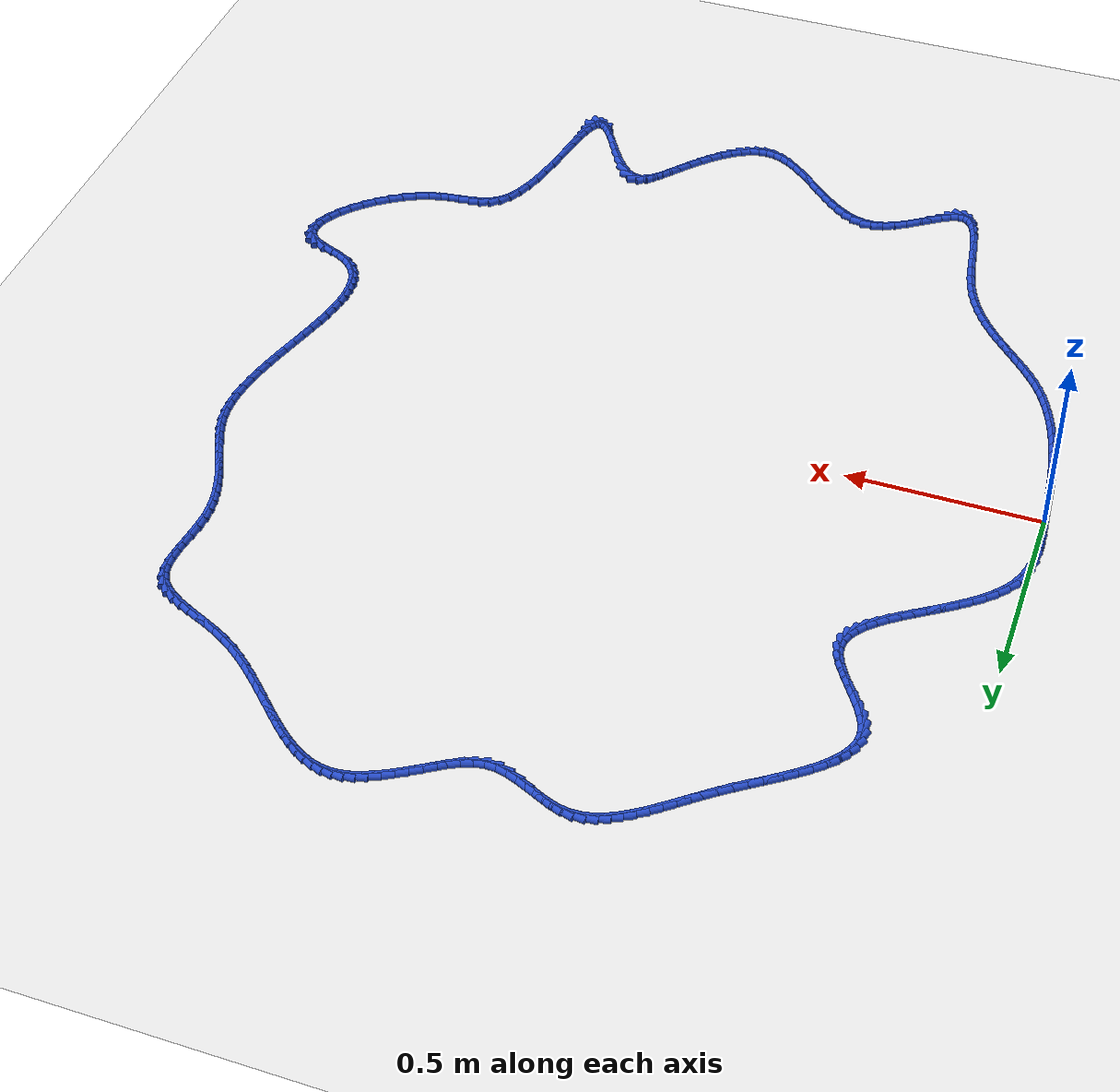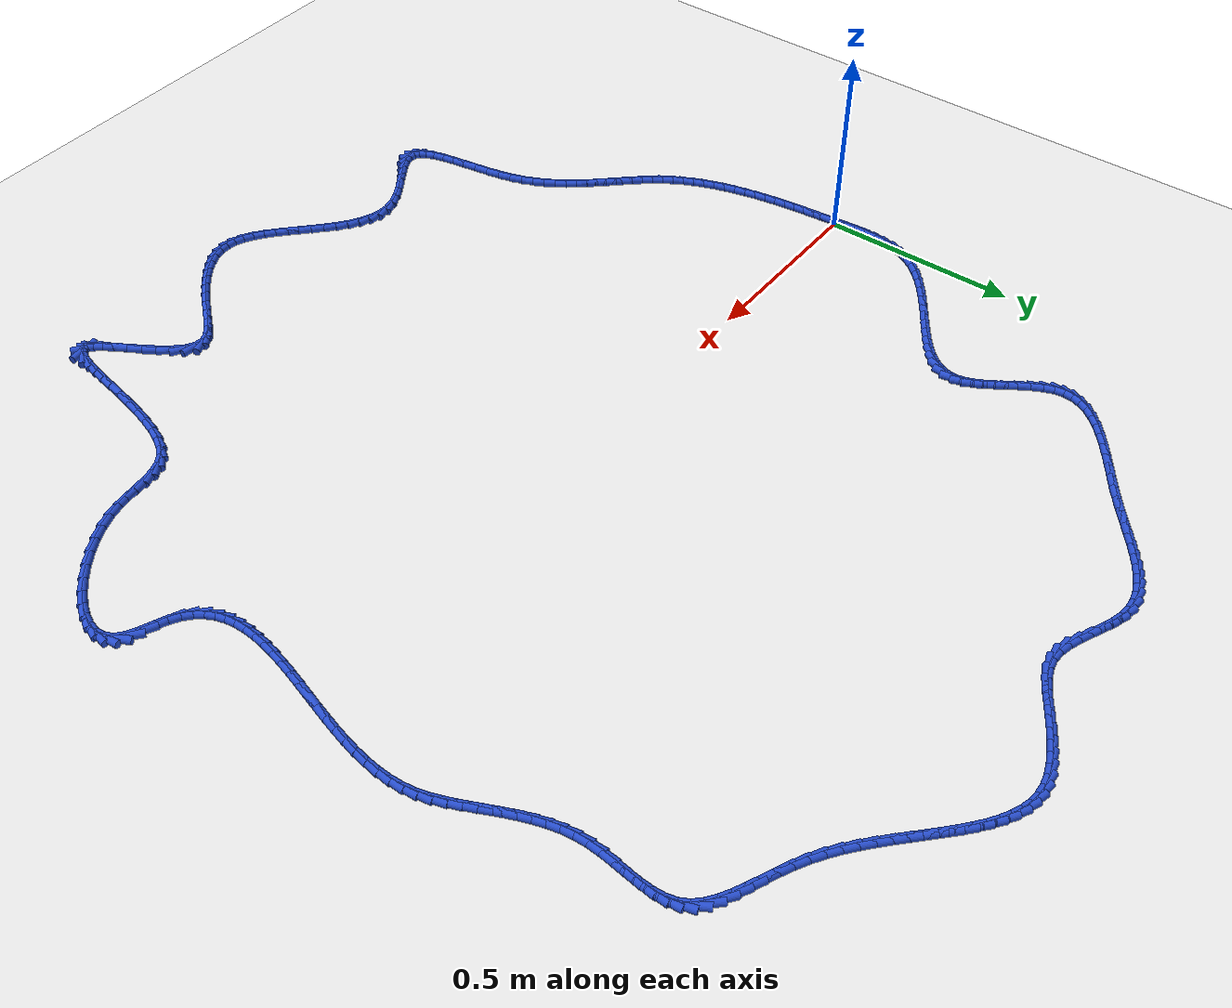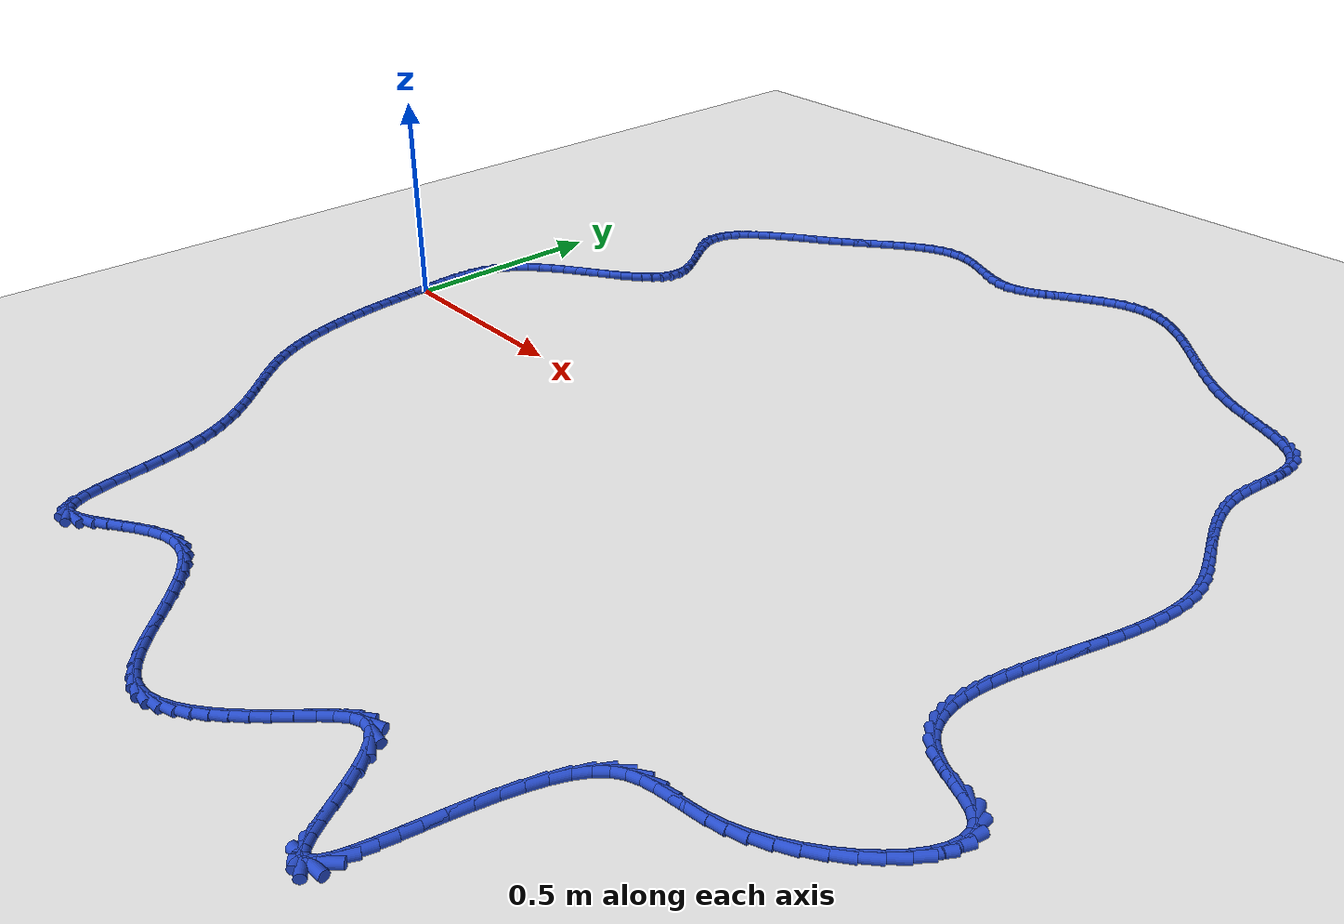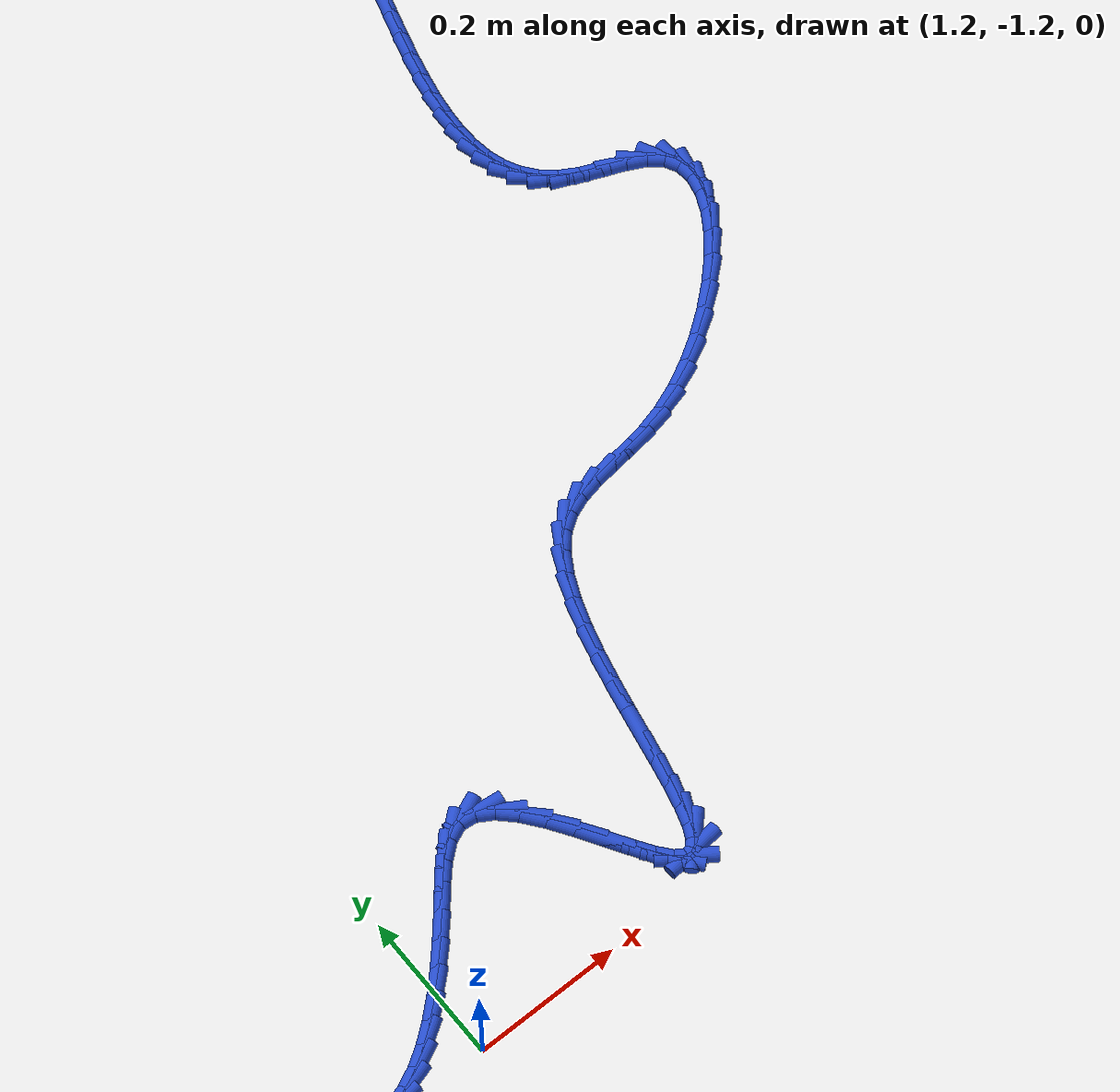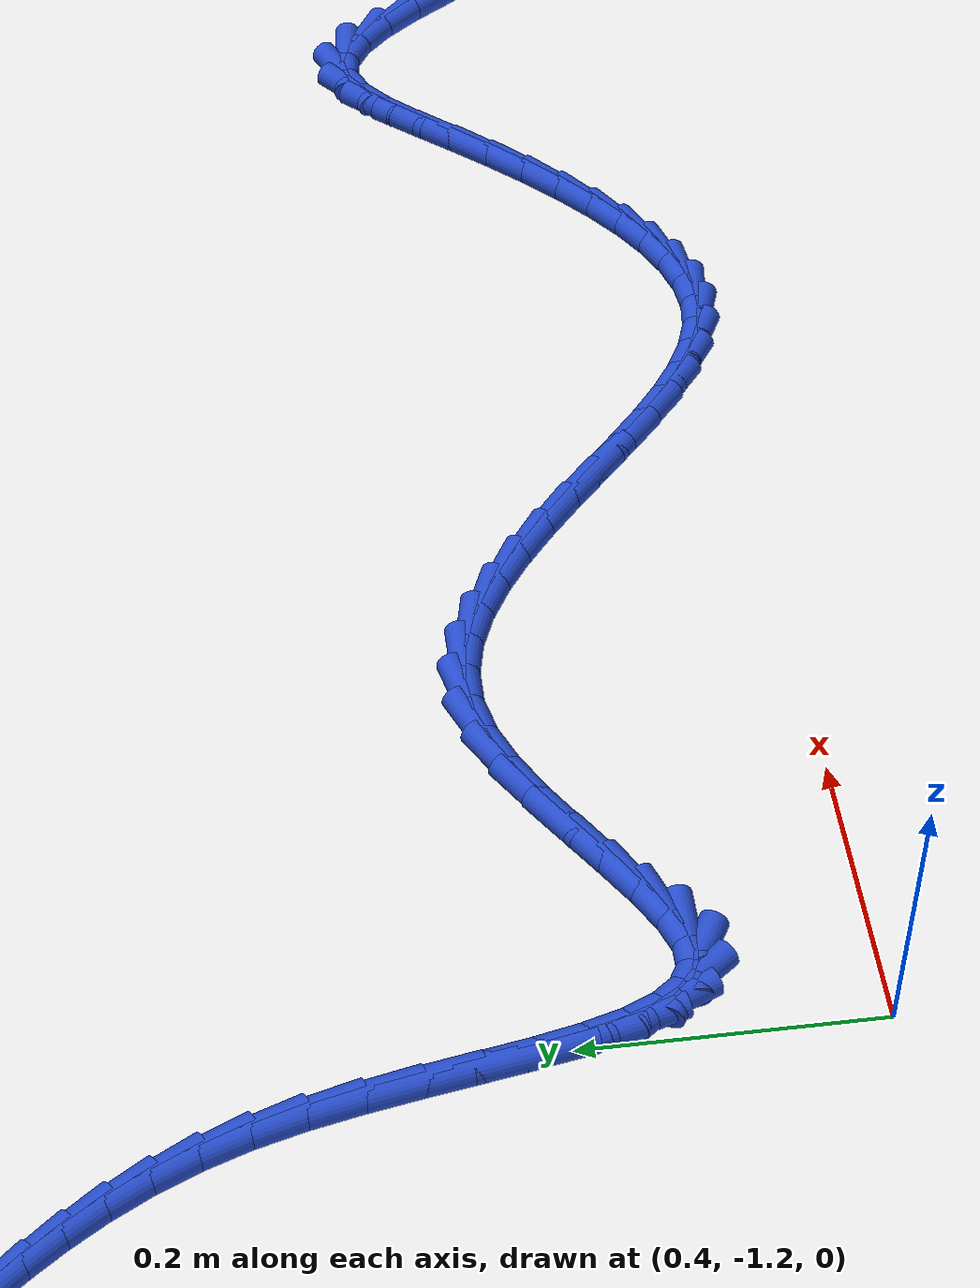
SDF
<sdf version="1.6">
 <world name="default">
  <light name="sun" type="directional">
   <pose>0 0 10 0 -0 0</pose>
   <diffuse>0.8 0.8 0.8 1</diffuse>
   <specular>0.2 0.2 0.2 1</specular>
   <attenuation>
    <range>1000</range>
    <constant>0.9</constant>
    <linear>0.01</linear>
    <quadratic>0.001</quadratic>
   </attenuation>
   <direction>-0.5 0.1 -0.9</direction>
  </light>
  <model name="ground_plane">
   <static>1</static>
   <link name="link">
    <collision name="collision">
     <geometry><plane><normal>0 0 1</normal><size>100 100</size></plane></geometry>
     <surface><friction><ode><mu>100</mu><mu2>50</mu2></ode></friction></surface>
    </collision>
    <visual name="visual">
     <cast_shadows>0</cast_shadows>
     <geometry><plane><normal>0 0 1</normal><size>100 100</size></plane></geometry>
     <material>
      <script><uri>file://media/materials/scripts/gazebo.material</uri><name>Gazebo/WhiteGlow</name></script>
     </material>
    </visual>
   </link>
  </model>
  <gravity>0 0 -9.8</gravity>
  <magnetic_field>6e-06 2.3e-05 -4.2e-05</magnetic_field>
  <atmosphere type="adiabatic"/>
  <physics name="default_physics" default="0" type="ode">
   <max_step_size>0.001</max_step_size>
   <real_time_factor>1</real_time_factor>
   <real_time_update_rate>1000</real_time_update_rate>
  </physics>
  <scene><ambient>0.4 0.4 0.4 1</ambient><background>0.7 0.7 0.7 1</background><shadows>1</shadows></scene>
  <spherical_coordinates>
   <surface_model>EARTH_WGS84</surface_model>
   <latitude_deg>0</latitude_deg>
   <longitude_deg>0</longitude_deg>
   <elevation>0</elevation>
   <heading_deg>0</heading_deg>
  </spherical_coordinates>
  <model name="line">
   <link name="link_0">
    <pose>-1.2576745200831851e-17 6.938893903907228e-18 0.01 0 1.57 -1.494866581217393</pose>
    <collision name="collision">
     <geometry><cylinder><radius>0.01</radius><length>0.08</length></cylinder></geometry>
    </collision>
    <visual name="visual">
     <material>
      <script><name>Gazebo/Blue</name><uri>file://media/materials/scripts/gazebo.material</uri></script>
     </material>
     <geometry><cylinder><radius>0.01</radius><length>0.08</length></cylinder></geometry>
    </visual>
   </link>
   <link name="link_1">
    <pose>-0.0022657340430550727 0.029782506438946674 0.01 0 1.57 -1.5117864989916552</pose>
    <collision name="collision">
     <geometry><cylinder><radius>0.01</radius><length>0.08</length></cylinder></geometry>
    </collision>
    <visual name="visual">
     <material>
      <script><name>Gazebo/Blue</name><uri>file://media/materials/scripts/gazebo.material</uri></script>
     </material>
     <geometry><cylinder><radius>0.01</radius><length>0.08</length></cylinder></geometry>
    </visual>
   </link>
   <link name="link_2">
    <pose>-0.0040357827391061755 0.059743510461020305 0.01 0 1.57 -1.5465241977232782</pose>
    <collision name="collision">
     <geometry><cylinder><radius>0.01</radius><length>0.08</length></cylinder></geometry>
    </collision>
    <visual name="visual">
     <material>
      <script><name>Gazebo/Blue</name><uri>file://media/materials/scripts/gazebo.material</uri></script>
     </material>
     <geometry><cylinder><radius>0.01</radius><length>0.08</length></cylinder></geometry>
    </visual>
   </link>
   <link name="link_3">
    <pose>-0.004761638501300378 0.08964254452626104 0.01 0 1.57 1.5415160338145841</pose>
    <collision name="collision">
     <geometry><cylinder><radius>0.01</radius><length>0.08</length></cylinder></geometry>
    </collision>
    <visual name="visual">
     <material>
      <script><name>Gazebo/Blue</name><uri>file://media/materials/scripts/gazebo.material</uri></script>
     </material>
     <geometry><cylinder><radius>0.01</radius><length>0.08</length></cylinder></geometry>
    </visual>
   </link>
   <link name="link_4">
    <pose>-0.003894793742784732 0.11923914109470891 0.01 0 1.57 1.4676296312365655</pose>
    <collision name="collision">
     <geometry><cylinder><radius>0.01</radius><length>0.08</length></cylinder></geometry>
    </collision>
    <visual name="visual">
     <material>
      <script><name>Gazebo/Blue</name><uri>file://media/materials/scripts/gazebo.material</uri></script>
     </material>
     <geometry><cylinder><radius>0.01</radius><length>0.08</length></cylinder></geometry>
    </visual>
   </link>
   <link name="link_5">
    <pose>-0.0008867408767062931 0.14829283262640403 0.01 0 1.57 1.37191471027893</pose>
    <collision name="collision">
     <geometry><cylinder><radius>0.01</radius><length>0.08</length></cylinder></geometry>
    </collision>
    <visual name="visual">
     <material>
      <script><name>Gazebo/Blue</name><uri>file://media/materials/scripts/gazebo.material</uri></script>
     </material>
     <geometry><cylinder><radius>0.01</radius><length>0.08</length></cylinder></geometry>
    </visual>
   </link>
   <link name="link_6">
    <pose>0.004811027683787888 0.17656315158138655 0.01 0 1.57 1.2538817009695729</pose>
    <collision name="collision">
     <geometry><cylinder><radius>0.01</radius><length>0.08</length></cylinder></geometry>
    </collision>
    <visual name="visual">
     <material>
      <script><name>Gazebo/Blue</name><uri>file://media/materials/scripts/gazebo.material</uri></script>
     </material>
     <geometry><cylinder><radius>0.01</radius><length>0.08</length></cylinder></geometry>
    </visual>
   </link>
   <link name="link_7">
    <pose>0.013747019525550757 0.20380963041969663 0.01 0 1.57 1.115445793027237</pose>
    <collision name="collision">
     <geometry><cylinder><radius>0.01</radius><length>0.08</length></cylinder></geometry>
    </collision>
    <visual name="visual">
     <material>
      <script><name>Gazebo/Blue</name><uri>file://media/materials/scripts/gazebo.material</uri></script>
     </material>
     <geometry><cylinder><radius>0.01</radius><length>0.08</length></cylinder></geometry>
    </visual>
   </link>
   <link name="link_8">
    <pose>0.026469742235435245 0.22979180160137413 0.01 0 1.57 0.9684534557032066</pose>
    <collision name="collision">
     <geometry><cylinder><radius>0.01</radius><length>0.08</length></cylinder></geometry>
    </collision>
    <visual name="visual">
     <material>
      <script><name>Gazebo/Blue</name><uri>file://media/materials/scripts/gazebo.material</uri></script>
     </material>
     <geometry><cylinder><radius>0.01</radius><length>0.08</length></cylinder></geometry>
    </visual>
   </link>
   <link name="link_9">
    <pose>0.043342757095608635 0.25433144988760825 0.01 0 1.57 0.8452526352798901</pose>
    <collision name="collision">
     <geometry><cylinder><radius>0.01</radius><length>0.08</length></cylinder></geometry>
    </collision>
    <visual name="visual">
     <material>
      <script><name>Gazebo/Blue</name><uri>file://media/materials/scripts/gazebo.material</uri></script>
     </material>
     <geometry><cylinder><radius>0.01</radius><length>0.08</length></cylinder></geometry>
    </visual>
   </link>
   <link name="link_10">
    <pose>0.06391367953497079 0.27752500465638674 0.01 0 1.57 0.7509488821139205</pose>
    <collision name="collision">
     <geometry><cylinder><radius>0.01</radius><length>0.08</length></cylinder></geometry>
    </collision>
    <visual name="visual">
     <material>
      <script><name>Gazebo/Blue</name><uri>file://media/materials/scripts/gazebo.material</uri></script>
     </material>
     <geometry><cylinder><radius>0.01</radius><length>0.08</length></cylinder></geometry>
    </visual>
   </link>
   <link name="link_11">
    <pose>0.0875051781719609 0.2995446116219125 0.01 0 1.57 0.6810572236037761</pose>
    <collision name="collision">
     <geometry><cylinder><radius>0.01</radius><length>0.08</length></cylinder></geometry>
    </collision>
    <visual name="visual">
     <material>
      <script><name>Gazebo/Blue</name><uri>file://media/materials/scripts/gazebo.material</uri></script>
     </material>
     <geometry><cylinder><radius>0.01</radius><length>0.08</length></cylinder></geometry>
    </visual>
   </link>
   <link name="link_12">
    <pose>0.11343991451883886 0.320562418890304 0.01 0 1.57 0.6315152533288507</pose>
    <collision name="collision">
     <geometry><cylinder><radius>0.01</radius><length>0.08</length></cylinder></geometry>
    </collision>
    <visual name="visual">
     <material>
      <script><name>Gazebo/Blue</name><uri>file://media/materials/scripts/gazebo.material</uri></script>
     </material>
     <geometry><cylinder><radius>0.01</radius><length>0.08</length></cylinder></geometry>
    </visual>
   </link>
   <link name="link_13">
    <pose>0.14104055008786476 0.34075057456767993 0.01 0 1.57 0.5993261322269449</pose>
    <collision name="collision">
     <geometry><cylinder><radius>0.01</radius><length>0.08</length></cylinder></geometry>
    </collision>
    <visual name="visual">
     <material>
      <script><name>Gazebo/Blue</name><uri>file://media/materials/scripts/gazebo.material</uri></script>
     </material>
     <geometry><cylinder><radius>0.01</radius><length>0.08</length></cylinder></geometry>
    </visual>
   </link>
   <link name="link_14">
    <pose>0.16962974639129857 0.3602812267601588 0.01 0 1.57 0.5826742077434577</pose>
    <collision name="collision">
     <geometry><cylinder><radius>0.01</radius><length>0.08</length></cylinder></geometry>
    </collision>
    <visual name="visual">
     <material>
      <script><name>Gazebo/Blue</name><uri>file://media/materials/scripts/gazebo.material</uri></script>
     </material>
     <geometry><cylinder><radius>0.01</radius><length>0.08</length></cylinder></geometry>
    </visual>
   </link>
   <link name="link_15">
    <pose>0.1985301649414002 0.3793265235738593 0.01 0 1.57 0.5809144257593694</pose>
    <collision name="collision">
     <geometry><cylinder><radius>0.01</radius><length>0.08</length></cylinder></geometry>
    </collision>
    <visual name="visual">
     <material>
      <script><name>Gazebo/Blue</name><uri>file://media/materials/scripts/gazebo.material</uri></script>
     </material>
     <geometry><cylinder><radius>0.01</radius><length>0.08</length></cylinder></geometry>
    </visual>
   </link>
   <link name="link_16">
    <pose>0.22706446725042975 0.3980586131149004 0.01 0 1.57 0.5946165105800073</pose>
    <collision name="collision">
     <geometry><cylinder><radius>0.01</radius><length>0.08</length></cylinder></geometry>
    </collision>
    <visual name="visual">
     <material>
      <script><name>Gazebo/Blue</name><uri>file://media/materials/scripts/gazebo.material</uri></script>
     </material>
     <geometry><cylinder><radius>0.01</radius><length>0.08</length></cylinder></geometry>
    </visual>
   </link>
   <link name="link_17">
    <pose>0.2545553148306471 0.41664964348940003 0.01 0 1.57 0.6257505566522185</pose>
    <collision name="collision">
     <geometry><cylinder><radius>0.01</radius><length>0.08</length></cylinder></geometry>
    </collision>
    <visual name="visual">
     <material>
      <script><name>Gazebo/Blue</name><uri>file://media/materials/scripts/gazebo.material</uri></script>
     </material>
     <geometry><cylinder><radius>0.01</radius><length>0.08</length></cylinder></geometry>
    </visual>
   </link>
   <link name="link_18">
    <pose>0.2803253691943123 0.4352717628034775 0.01 0 1.57 0.6780667402587</pose>
    <collision name="collision">
     <geometry><cylinder><radius>0.01</radius><length>0.08</length></cylinder></geometry>
    </collision>
    <visual name="visual">
     <material>
      <script><name>Gazebo/Blue</name><uri>file://media/materials/scripts/gazebo.material</uri></script>
     </material>
     <geometry><cylinder><radius>0.01</radius><length>0.08</length></cylinder></geometry>
    </visual>
   </link>
   <link name="link_19">
    <pose>0.30369729185368527 0.4540971191632512 0.01 0 1.57 0.7576637880578666</pose>
    <collision name="collision">
     <geometry><cylinder><radius>0.01</radius><length>0.08</length></cylinder></geometry>
    </collision>
    <visual name="visual">
     <material>
      <script><name>Gazebo/Blue</name><uri>file://media/materials/scripts/gazebo.material</uri></script>
     </material>
     <geometry><cylinder><radius>0.01</radius><length>0.08</length></cylinder></geometry>
    </visual>
   </link>
   <link name="link_20">
    <pose>0.323993744321026 0.4732978606748395 0.01 0 1.57 0.8734712346691922</pose>
    <collision name="collision">
     <geometry><cylinder><radius>0.01</radius><length>0.08</length></cylinder></geometry>
    </collision>
    <visual name="visual">
     <material>
      <script><name>Gazebo/Blue</name><uri>file://media/materials/scripts/gazebo.material</uri></script>
     </material>
     <geometry><cylinder><radius>0.01</radius><length>0.08</length></cylinder></geometry>
    </visual>
   </link>
   <link name="link_21">
    <pose>0.34053738810859463 0.49304613544436127 0.01 0 1.57 1.036407786492608</pose>
    <collision name="collision">
     <geometry><cylinder><radius>0.01</radius><length>0.08</length></cylinder></geometry>
    </collision>
    <visual name="visual">
     <material>
      <script><name>Gazebo/Blue</name><uri>file://media/materials/scripts/gazebo.material</uri></script>
     </material>
     <geometry><cylinder><radius>0.01</radius><length>0.08</length></cylinder></geometry>
    </visual>
   </link>
   <link name="link_22">
    <pose>0.35265088472865097 0.5135140915779353 0.01 0 1.57 1.2538533732736625</pose>
    <collision name="collision">
     <geometry><cylinder><radius>0.01</radius><length>0.08</length></cylinder></geometry>
    </collision>
    <visual name="visual">
     <material>
      <script><name>Gazebo/Blue</name><uri>file://media/materials/scripts/gazebo.material</uri></script>
     </material>
     <geometry><cylinder><radius>0.01</radius><length>0.08</length></cylinder></geometry>
    </visual>
   </link>
   <link name="link_23">
    <pose>0.35965689569345494 0.5348738771816798 0.01 0 1.57 1.5163905753766793</pose>
    <collision name="collision">
     <geometry><cylinder><radius>0.01</radius><length>0.08</length></cylinder></geometry>
    </collision>
    <visual name="visual">
     <material>
      <script><name>Gazebo/Blue</name><uri>file://media/materials/scripts/gazebo.material</uri></script>
     </material>
     <geometry><cylinder><radius>0.01</radius><length>0.08</length></cylinder></geometry>
    </visual>
   </link>
   <link name="link_24">
    <pose>0.3608780825152668 0.5572976403617137 0.01 0 1.57 -1.356409938980425</pose>
    <collision name="collision">
     <geometry><cylinder><radius>0.01</radius><length>0.08</length></cylinder></geometry>
    </collision>
    <visual name="visual">
     <material>
      <script><name>Gazebo/Blue</name><uri>file://media/materials/scripts/gazebo.material</uri></script>
     </material>
     <geometry><cylinder><radius>0.01</radius><length>0.08</length></cylinder></geometry>
    </visual>
   </link>
   <link name="link_25">
    <pose>0.3557306147727348 0.5809388951609028 0.01 0 1.57 -1.1592149447651108</pose>
    <collision name="collision">
     <geometry><cylinder><radius>0.01</radius><length>0.08</length></cylinder></geometry>
    </collision>
    <visual name="visual">
     <material>
      <script><name>Gazebo/Blue</name><uri>file://media/materials/scripts/gazebo.material</uri></script>
     </material>
     <geometry><cylinder><radius>0.01</radius><length>0.08</length></cylinder></geometry>
    </visual>
   </link>
   <link name="link_26">
    <pose>0.34492504212954866 0.6056932146624767 0.01 0 1.57 -1.0459596506561195</pose>
    <collision name="collision">
     <geometry><cylinder><radius>0.01</radius><length>0.08</length></cylinder></geometry>
    </collision>
    <visual name="visual">
     <material>
      <script><name>Gazebo/Blue</name><uri>file://media/materials/scripts/gazebo.material</uri></script>
     </material>
     <geometry><cylinder><radius>0.01</radius><length>0.08</length></cylinder></geometry>
    </visual>
   </link>
   <link name="link_27">
    <pose>0.3301173218746331 0.6312677733850403 0.01 0 1.57 -0.9898856624915686</pose>
    <collision name="collision">
     <geometry><cylinder><radius>0.01</radius><length>0.08</length></cylinder></geometry>
    </collision>
    <visual name="visual">
     <material>
      <script><name>Gazebo/Blue</name><uri>file://media/materials/scripts/gazebo.material</uri></script>
     </material>
     <geometry><cylinder><radius>0.01</radius><length>0.08</length></cylinder></geometry>
    </visual>
   </link>
   <link name="link_28">
    <pose>0.3129849581739691 0.6573654520372059 0.01 0 1.57 -0.9767591322554221</pose>
    <collision name="collision">
     <geometry><cylinder><radius>0.01</radius><length>0.08</length></cylinder></geometry>
    </collision>
    <visual name="visual">
     <material>
      <script><name>Gazebo/Blue</name><uri>file://media/materials/scripts/gazebo.material</uri></script>
     </material>
     <geometry><cylinder><radius>0.01</radius><length>0.08</length></cylinder></geometry>
    </visual>
   </link>
   <link name="link_29">
    <pose>0.2952054551935364 0.6836891313275839 0.01 0 1.57 -1.0029031472028256</pose>
    <collision name="collision">
     <geometry><cylinder><radius>0.01</radius><length>0.08</length></cylinder></geometry>
    </collision>
    <visual name="visual">
     <material>
      <script><name>Gazebo/Blue</name><uri>file://media/materials/scripts/gazebo.material</uri></script>
     </material>
     <geometry><cylinder><radius>0.01</radius><length>0.08</length></cylinder></geometry>
    </visual>
   </link>
   <link name="link_30">
    <pose>0.27845631709931545 0.7099416919647864 0.01 0 1.57 -1.0737586363526332</pose>
    <collision name="collision">
     <geometry><cylinder><radius>0.01</radius><length>0.08</length></cylinder></geometry>
    </collision>
    <visual name="visual">
     <material>
      <script><name>Gazebo/Blue</name><uri>file://media/materials/scripts/gazebo.material</uri></script>
     </material>
     <geometry><cylinder><radius>0.01</radius><length>0.08</length></cylinder></geometry>
    </visual>
   </link>
   <link name="link_31">
    <pose>0.2644150480572868 0.735826014657425 0.01 0 1.57 -1.2051331066957656</pose>
    <collision name="collision">
     <geometry><cylinder><radius>0.01</radius><length>0.08</length></cylinder></geometry>
    </collision>
    <visual name="visual">
     <material>
      <script><name>Gazebo/Blue</name><uri>file://media/materials/scripts/gazebo.material</uri></script>
     </material>
     <geometry><cylinder><radius>0.01</radius><length>0.08</length></cylinder></geometry>
    </visual>
   </link>
   <link name="link_32">
    <pose>0.2547591522334305 0.7610449801141108 0.01 0 1.57 -1.417647684400381</pose>
    <collision name="collision">
     <geometry><cylinder><radius>0.01</radius><length>0.08</length></cylinder></geometry>
    </collision>
    <visual name="visual">
     <material>
      <script><name>Gazebo/Blue</name><uri>file://media/materials/scripts/gazebo.material</uri></script>
     </material>
     <geometry><cylinder><radius>0.01</radius><length>0.08</length></cylinder></geometry>
    </visual>
   </link>
   <link name="link_33">
    <pose>0.2510105877549419 0.7853299596103389 0.01 0 1.57 1.4728865628770562</pose>
    <collision name="collision">
     <geometry><cylinder><radius>0.01</radius><length>0.08</length></cylinder></geometry>
    </collision>
    <visual name="visual">
     <material>
      <script><name>Gazebo/Blue</name><uri>file://media/materials/scripts/gazebo.material</uri></script>
     </material>
     <geometry><cylinder><radius>0.01</radius><length>0.08</length></cylinder></geometry>
    </visual>
   </link>
   <link name="link_34">
    <pose>0.2533028069257572 0.808666649882633 0.01 0 1.57 1.2397201899270875</pose>
    <collision name="collision">
     <geometry><cylinder><radius>0.01</radius><length>0.08</length></cylinder></geometry>
    </collision>
    <visual name="visual">
     <material>
      <script><name>Gazebo/Blue</name><uri>file://media/materials/scripts/gazebo.material</uri></script>
     </material>
     <geometry><cylinder><radius>0.01</radius><length>0.08</length></cylinder></geometry>
    </visual>
   </link>
   <link name="link_35">
    <pose>0.26103935809138784 0.8311744404166769 0.01 0 1.57 1.047472549642019</pose>
    <collision name="collision">
     <geometry><cylinder><radius>0.01</radius><length>0.08</length></cylinder></geometry>
    </collision>
    <visual name="visual">
     <material>
      <script><name>Gazebo/Blue</name><uri>file://media/materials/scripts/gazebo.material</uri></script>
     </material>
     <geometry><cylinder><radius>0.01</radius><length>0.08</length></cylinder></geometry>
    </visual>
   </link>
   <link name="link_36">
    <pose>0.27361729595879836 0.8529739101044843 0.01 0 1.57 0.900469135109178</pose>
    <collision name="collision">
     <geometry><cylinder><radius>0.01</radius><length>0.08</length></cylinder></geometry>
    </collision>
    <visual name="visual">
     <material>
      <script><name>Gazebo/Blue</name><uri>file://media/materials/scripts/gazebo.material</uri></script>
     </material>
     <geometry><cylinder><radius>0.01</radius><length>0.08</length></cylinder></geometry>
    </visual>
   </link>
   <link name="link_37">
    <pose>0.29043367523495317 0.8741856378380694 0.01 0 1.57 0.792502766477532</pose>
    <collision name="collision">
     <geometry><cylinder><radius>0.01</radius><length>0.08</length></cylinder></geometry>
    </collision>
    <visual name="visual">
     <material>
      <script><name>Gazebo/Blue</name><uri>file://media/materials/scripts/gazebo.material</uri></script>
     </material>
     <geometry><cylinder><radius>0.01</radius><length>0.08</length></cylinder></geometry>
    </visual>
   </link>
   <link name="link_38">
    <pose>0.3108855506268169 0.8949302025094461 0.01 0 1.57 0.7151793328294161</pose>
    <collision name="collision">
     <geometry><cylinder><radius>0.01</radius><length>0.08</length></cylinder></geometry>
    </collision>
    <visual name="visual">
     <material>
      <script><name>Gazebo/Blue</name><uri>file://media/materials/scripts/gazebo.material</uri></script>
     </material>
     <geometry><cylinder><radius>0.01</radius><length>0.08</length></cylinder></geometry>
    </visual>
   </link>
   <link name="link_39">
    <pose>0.334369976841354 0.9153281830106287 0.01 0 1.57 0.6614425886220949</pose>
    <collision name="collision">
     <geometry><cylinder><radius>0.01</radius><length>0.08</length></cylinder></geometry>
    </collision>
    <visual name="visual">
     <material>
      <script><name>Gazebo/Blue</name><uri>file://media/materials/scripts/gazebo.material</uri></script>
     </material>
     <geometry><cylinder><radius>0.01</radius><length>0.08</length></cylinder></geometry>
    </visual>
   </link>
   <link name="link_40">
    <pose>0.36028400858552884 0.9355001582336313 0.01 0 1.57 0.6262333762164071</pose>
    <collision name="collision">
     <geometry><cylinder><radius>0.01</radius><length>0.08</length></cylinder></geometry>
    </collision>
    <visual name="visual">
     <material>
      <script><name>Gazebo/Blue</name><uri>file://media/materials/scripts/gazebo.material</uri></script>
     </material>
     <geometry><cylinder><radius>0.01</radius><length>0.08</length></cylinder></geometry>
    </visual>
   </link>
   <link name="link_41">
    <pose>0.38802470056630634 0.955566707070468 0.01 0 1.57 0.6062309616112145</pose>
    <collision name="collision">
     <geometry><cylinder><radius>0.01</radius><length>0.08</length></cylinder></geometry>
    </collision>
    <visual name="visual">
     <material>
      <script><name>Gazebo/Blue</name><uri>file://media/materials/scripts/gazebo.material</uri></script>
     </material>
     <geometry><cylinder><radius>0.01</radius><length>0.08</length></cylinder></geometry>
    </visual>
   </link>
   <link name="link_42">
    <pose>0.4169891074906508 0.9756484084131528 0.01 0 1.57 0.5994731163087782</pose>
    <collision name="collision">
     <geometry><cylinder><radius>0.01</radius><length>0.08</length></cylinder></geometry>
    </collision>
    <visual name="visual">
     <material>
      <script><name>Gazebo/Blue</name><uri>file://media/materials/scripts/gazebo.material</uri></script>
     </material>
     <geometry><cylinder><radius>0.01</radius><length>0.08</length></cylinder></geometry>
    </visual>
   </link>
   <link name="link_43">
    <pose>0.4465742840655268 0.9958658411537 0.01 0 1.57 0.6050731336399192</pose>
    <collision name="collision">
     <geometry><cylinder><radius>0.01</radius><length>0.08</length></cylinder></geometry>
    </collision>
    <visual name="visual">
     <material>
      <script><name>Gazebo/Blue</name><uri>file://media/materials/scripts/gazebo.material</uri></script>
     </material>
     <geometry><cylinder><radius>0.01</radius><length>0.08</length></cylinder></geometry>
    </visual>
   </link>
   <link name="link_44">
    <pose>0.4761772849978988 1.0163395841841234 0.01 0 1.57 0.6230512626197703</pose>
    <collision name="collision">
     <geometry><cylinder><radius>0.01</radius><length>0.08</length></cylinder></geometry>
    </collision>
    <visual name="visual">
     <material>
      <script><name>Gazebo/Blue</name><uri>file://media/materials/scripts/gazebo.material</uri></script>
     </material>
     <geometry><cylinder><radius>0.01</radius><length>0.08</length></cylinder></geometry>
    </visual>
   </link>
   <link name="link_45">
    <pose>0.5051955370347525 1.037189937215831 0.01 0 1.57 0.6479190353864179</pose>
    <collision name="collision">
     <geometry><cylinder><radius>0.01</radius><length>0.08</length></cylinder></geometry>
    </collision>
    <visual name="visual">
     <material>
      <script><name>Gazebo/Blue</name><uri>file://media/materials/scripts/gazebo.material</uri></script>
     </material>
     <geometry><cylinder><radius>0.01</radius><length>0.08</length></cylinder></geometry>
    </visual>
   </link>
   <link name="link_46">
    <pose>0.5332130936363997 1.0583971543844672 0.01 0 1.57 0.6635186357237746</pose>
    <collision name="collision">
     <geometry><cylinder><radius>0.01</radius><length>0.08</length></cylinder></geometry>
    </collision>
    <visual name="visual">
     <material>
      <script><name>Gazebo/Blue</name><uri>file://media/materials/scripts/gazebo.material</uri></script>
     </material>
     <geometry><cylinder><radius>0.01</radius><length>0.08</length></cylinder></geometry>
    </visual>
   </link>
   <link name="link_47">
    <pose>0.5603027593396834 1.0795747286868362 0.01 0 1.57 0.6666066748385984</pose>
    <collision name="collision">
     <geometry><cylinder><radius>0.01</radius><length>0.08</length></cylinder></geometry>
    </collision>
    <visual name="visual">
     <material>
      <script><name>Gazebo/Blue</name><uri>file://media/materials/scripts/gazebo.material</uri></script>
     </material>
     <geometry><cylinder><radius>0.01</radius><length>0.08</length></cylinder></geometry>
    </visual>
   </link>
   <link name="link_48">
    <pose>0.5866163682679847 1.100276848941085 0.01 0 1.57 0.6561793922529283</pose>
    <collision name="collision">
     <geometry><cylinder><radius>0.01</radius><length>0.08</length></cylinder></geometry>
    </collision>
    <visual name="visual">
     <material>
      <script><name>Gazebo/Blue</name><uri>file://media/materials/scripts/gazebo.material</uri></script>
     </material>
     <geometry><cylinder><radius>0.01</radius><length>0.08</length></cylinder></geometry>
    </visual>
   </link>
   <link name="link_49">
    <pose>0.6123057545446843 1.1200577039653603 0.01 0 1.57 0.6307166704881026</pose>
    <collision name="collision">
     <geometry><cylinder><radius>0.01</radius><length>0.08</length></cylinder></geometry>
    </collision>
    <visual name="visual">
     <material>
      <script><name>Gazebo/Blue</name><uri>file://media/materials/scripts/gazebo.material</uri></script>
     </material>
     <geometry><cylinder><radius>0.01</radius><length>0.08</length></cylinder></geometry>
    </visual>
   </link>
   <link name="link_50">
    <pose>0.6375227522931634 1.13847148257781 0.01 0 1.57 0.5880933095271511</pose>
    <collision name="collision">
     <geometry><cylinder><radius>0.01</radius><length>0.08</length></cylinder></geometry>
    </collision>
    <visual name="visual">
     <material>
      <script><name>Gazebo/Blue</name><uri>file://media/materials/scripts/gazebo.material</uri></script>
     </material>
     <geometry><cylinder><radius>0.01</radius><length>0.08</length></cylinder></geometry>
    </visual>
   </link>
   <link name="link_51">
    <pose>0.6624191956368031 1.1550723735965815 0.01 0 1.57 0.5255872089880135</pose>
    <collision name="collision">
     <geometry><cylinder><radius>0.01</radius><length>0.08</length></cylinder></geometry>
    </collision>
    <visual name="visual">
     <material>
      <script><name>Gazebo/Blue</name><uri>file://media/materials/scripts/gazebo.material</uri></script>
     </material>
     <geometry><cylinder><radius>0.01</radius><length>0.08</length></cylinder></geometry>
    </visual>
   </link>
   <link name="link_52">
    <pose>0.6871469186989846 1.1694145658398227 0.01 0 1.57 0.4401424813250403</pose>
    <collision name="collision">
     <geometry><cylinder><radius>0.01</radius><length>0.08</length></cylinder></geometry>
    </collision>
    <visual name="visual">
     <material>
      <script><name>Gazebo/Blue</name><uri>file://media/materials/scripts/gazebo.material</uri></script>
     </material>
     <geometry><cylinder><radius>0.01</radius><length>0.08</length></cylinder></geometry>
    </visual>
   </link>
   <link name="link_53">
    <pose>0.711857755603089 1.18105224812568 0.01 0 1.57 0.32917349159626663</pose>
    <collision name="collision">
     <geometry><cylinder><radius>0.01</radius><length>0.08</length></cylinder></geometry>
    </collision>
    <visual name="visual">
     <material>
      <script><name>Gazebo/Blue</name><uri>file://media/materials/scripts/gazebo.material</uri></script>
     </material>
     <geometry><cylinder><radius>0.01</radius><length>0.08</length></cylinder></geometry>
    </visual>
   </link>
   <link name="link_54">
    <pose>0.736703540472497 1.1895396092723014 0.01 0 1.57 0.19221443596110152</pose>
    <collision name="collision">
     <geometry><cylinder><radius>0.01</radius><length>0.08</length></cylinder></geometry>
    </collision>
    <visual name="visual">
     <material>
      <script><name>Gazebo/Blue</name><uri>file://media/materials/scripts/gazebo.material</uri></script>
     </material>
     <geometry><cylinder><radius>0.01</radius><length>0.08</length></cylinder></geometry>
    </visual>
   </link>
   <link name="link_55">
    <pose>0.7618361074305899 1.194430838097834 0.01 0 1.57 0.033200389983007776</pose>
    <collision name="collision">
     <geometry><cylinder><radius>0.01</radius><length>0.08</length></cylinder></geometry>
    </collision>
    <visual name="visual">
     <material>
      <script><name>Gazebo/Blue</name><uri>file://media/materials/scripts/gazebo.material</uri></script>
     </material>
     <geometry><cylinder><radius>0.01</radius><length>0.08</length></cylinder></geometry>
    </visual>
   </link>
   <link name="link_56">
    <pose>0.787407290600749 1.1952801234204251 0.01 0 1.57 -0.13815578577038984</pose>
    <collision name="collision">
     <geometry><cylinder><radius>0.01</radius><length>0.08</length></cylinder></geometry>
    </collision>
    <visual name="visual">
     <material>
      <script><name>Gazebo/Blue</name><uri>file://media/materials/scripts/gazebo.material</uri></script>
     </material>
     <geometry><cylinder><radius>0.01</radius><length>0.08</length></cylinder></geometry>
    </visual>
   </link>
   <link name="link_57">
    <pose>0.8135687762851693 1.1916425900808707 0.01 0 1.57 -0.2917829945881949</pose>
    <collision name="collision">
     <geometry><cylinder><radius>0.01</radius><length>0.08</length></cylinder></geometry>
    </collision>
    <visual name="visual">
     <material>
      <script><name>Gazebo/Blue</name><uri>file://media/materials/scripts/gazebo.material</uri></script>
     </material>
     <geometry><cylinder><radius>0.01</radius><length>0.08</length></cylinder></geometry>
    </visual>
   </link>
   <link name="link_58">
    <pose>0.8403912433967284 1.1835863120677006 0.01 0 1.57 -0.3839586581489926</pose>
    <collision name="collision">
     <geometry><cylinder><radius>0.01</radius><length>0.08</length></cylinder></geometry>
    </collision>
    <visual name="visual">
     <material>
      <script><name>Gazebo/Blue</name><uri>file://media/materials/scripts/gazebo.material</uri></script>
     </material>
     <geometry><cylinder><radius>0.01</radius><length>0.08</length></cylinder></geometry>
    </visual>
   </link>
   <link name="link_59">
    <pose>0.867730327855679 1.1725410430966854 0.01 0 1.57 -0.4206540215104794</pose>
    <collision name="collision">
     <geometry><cylinder><radius>0.01</radius><length>0.08</length></cylinder></geometry>
    </collision>
    <visual name="visual">
     <material>
      <script><name>Gazebo/Blue</name><uri>file://media/materials/scripts/gazebo.material</uri></script>
     </material>
     <geometry><cylinder><radius>0.01</radius><length>0.08</length></cylinder></geometry>
    </visual>
   </link>
   <link name="link_60">
    <pose>0.8954063814508796 1.160159960515433 0.01 0 1.57 -0.40898616554600187</pose>
    <collision name="collision">
     <geometry><cylinder><radius>0.01</radius><length>0.08</length></cylinder></geometry>
    </collision>
    <visual name="visual">
     <material>
      <script><name>Gazebo/Blue</name><uri>file://media/materials/scripts/gazebo.material</uri></script>
     </material>
     <geometry><cylinder><radius>0.01</radius><length>0.08</length></cylinder></geometry>
    </visual>
   </link>
   <link name="link_61">
    <pose>0.9232397559711888 1.1480962416715523 0.01 0 1.57 -0.3481379189393007</pose>
    <collision name="collision">
     <geometry><cylinder><radius>0.01</radius><length>0.08</length></cylinder></geometry>
    </collision>
    <visual name="visual">
     <material>
      <script><name>Gazebo/Blue</name><uri>file://media/materials/scripts/gazebo.material</uri></script>
     </material>
     <geometry><cylinder><radius>0.01</radius><length>0.08</length></cylinder></geometry>
    </visual>
   </link>
   <link name="link_62">
    <pose>0.9510508032054658 1.1380030639126522 0.01 0 1.57 -0.2301709402388039</pose>
    <collision name="collision">
     <geometry><cylinder><radius>0.01</radius><length>0.08</length></cylinder></geometry>
    </collision>
    <visual name="visual">
     <material>
      <script><name>Gazebo/Blue</name><uri>file://media/materials/scripts/gazebo.material</uri></script>
     </material>
     <geometry><cylinder><radius>0.01</radius><length>0.08</length></cylinder></geometry>
    </visual>
   </link>
   <link name="link_63">
    <pose>0.9786598749425691 1.1315336045863407 0.01 0 1.57 -0.04394819975968963</pose>
    <collision name="collision">
     <geometry><cylinder><radius>0.01</radius><length>0.08</length></cylinder></geometry>
    </collision>
    <visual name="visual">
     <material>
      <script><name>Gazebo/Blue</name><uri>file://media/materials/scripts/gazebo.material</uri></script>
     </material>
     <geometry><cylinder><radius>0.01</radius><length>0.08</length></cylinder></geometry>
    </visual>
   </link>
   <link name="link_64">
    <pose>1.0058878902262869 1.1303362113328674 0.01 0 1.57 0.17918037148259092</pose>
    <collision name="collision">
     <geometry><cylinder><radius>0.01</radius><length>0.08</length></cylinder></geometry>
    </collision>
    <visual name="visual">
     <material>
      <script><name>Gazebo/Blue</name><uri>file://media/materials/scripts/gazebo.material</uri></script>
     </material>
     <geometry><cylinder><radius>0.01</radius><length>0.08</length></cylinder></geometry>
    </visual>
   </link>
   <link name="link_65">
    <pose>1.0326584508983496 1.1351849725502725 0.01 0 1.57 0.35430926838815036</pose>
    <collision name="collision">
     <geometry><cylinder><radius>0.01</radius><length>0.08</length></cylinder></geometry>
    </collision>
    <visual name="visual">
     <material>
      <script><name>Gazebo/Blue</name><uri>file://media/materials/scripts/gazebo.material</uri></script>
     </material>
     <geometry><cylinder><radius>0.01</radius><length>0.08</length></cylinder></geometry>
    </visual>
   </link>
   <link name="link_66">
    <pose>1.0591161750923164 1.1449722053985454 0.01 0 1.57 0.4701508234432822</pose>
    <collision name="collision">
     <geometry><cylinder><radius>0.01</radius><length>0.08</length></cylinder></geometry>
    </collision>
    <visual name="visual">
     <material>
      <script><name>Gazebo/Blue</name><uri>file://media/materials/scripts/gazebo.material</uri></script>
     </material>
     <geometry><cylinder><radius>0.01</radius><length>0.08</length></cylinder></geometry>
    </visual>
   </link>
   <link name="link_67">
    <pose>1.0854343720507993 1.1583459459335204 0.01 0 1.57 0.5347386982467041</pose>
    <collision name="collision">
     <geometry><cylinder><radius>0.01</radius><length>0.08</length></cylinder></geometry>
    </collision>
    <visual name="visual">
     <material>
      <script><name>Gazebo/Blue</name><uri>file://media/materials/scripts/gazebo.material</uri></script>
     </material>
     <geometry><cylinder><radius>0.01</radius><length>0.08</length></cylinder></geometry>
    </visual>
   </link>
   <link name="link_68">
    <pose>1.1117863510164108 1.1739542302110304 0.01 0 1.57 0.5556560296867223</pose>
    <collision name="collision">
     <geometry><cylinder><radius>0.01</radius><length>0.08</length></cylinder></geometry>
    </collision>
    <visual name="visual">
     <material>
      <script><name>Gazebo/Blue</name><uri>file://media/materials/scripts/gazebo.material</uri></script>
     </material>
     <geometry><cylinder><radius>0.01</radius><length>0.08</length></cylinder></geometry>
    </visual>
   </link>
   <link name="link_69">
    <pose>1.1383454027439248 1.1904451304575354 0.01 0 1.57 0.5417903727069455</pose>
    <collision name="collision">
     <geometry><cylinder><radius>0.01</radius><length>0.08</length></cylinder></geometry>
    </collision>
    <visual name="visual">
     <material>
      <script><name>Gazebo/Blue</name><uri>file://media/materials/scripts/gazebo.material</uri></script>
     </material>
     <geometry><cylinder><radius>0.01</radius><length>0.08</length></cylinder></geometry>
    </visual>
   </link>
   <link name="link_70">
    <pose>1.1652096407270212 1.2066137998320758 0.01 0 1.57 0.5102517042248358</pose>
    <collision name="collision">
     <geometry><cylinder><radius>0.01</radius><length>0.08</length></cylinder></geometry>
    </collision>
    <visual name="visual">
     <material>
      <script><name>Gazebo/Blue</name><uri>file://media/materials/scripts/gazebo.material</uri></script>
     </material>
     <geometry><cylinder><radius>0.01</radius><length>0.08</length></cylinder></geometry>
    </visual>
   </link>
   <link name="link_71">
    <pose>1.1922308669606012 1.2217372888708997 0.01 0 1.57 0.4625818086852476</pose>
    <collision name="collision">
     <geometry><cylinder><radius>0.01</radius><length>0.08</length></cylinder></geometry>
    </collision>
    <visual name="visual">
     <material>
      <script><name>Gazebo/Blue</name><uri>file://media/materials/scripts/gazebo.material</uri></script>
     </material>
     <geometry><cylinder><radius>0.01</radius><length>0.08</length></cylinder></geometry>
    </visual>
   </link>
   <link name="link_72">
    <pose>1.2192105163539373 1.2351911890496001 0.01 0 1.57 0.39537862089625914</pose>
    <collision name="collision">
     <geometry><cylinder><radius>0.01</radius><length>0.08</length></cylinder></geometry>
    </collision>
    <visual name="visual">
     <material>
      <script><name>Gazebo/Blue</name><uri>file://media/materials/scripts/gazebo.material</uri></script>
     </material>
     <geometry><cylinder><radius>0.01</radius><length>0.08</length></cylinder></geometry>
    </visual>
   </link>
   <link name="link_73">
    <pose>1.2459500238163024 1.2463510918437704 0.01 0 1.57 0.30366394213907316</pose>
    <collision name="collision">
     <geometry><cylinder><radius>0.01</radius><length>0.08</length></cylinder></geometry>
    </collision>
    <visual name="visual">
     <material>
      <script><name>Gazebo/Blue</name><uri>file://media/materials/scripts/gazebo.material</uri></script>
     </material>
     <geometry><cylinder><radius>0.01</radius><length>0.08</length></cylinder></geometry>
    </visual>
   </link>
   <link name="link_74">
    <pose>1.2722508242569677 1.254592588729003 0.01 0 1.57 0.1810823473494174</pose>
    <collision name="collision">
     <geometry><cylinder><radius>0.01</radius><length>0.08</length></cylinder></geometry>
    </collision>
    <visual name="visual">
     <material>
      <script><name>Gazebo/Blue</name><uri>file://media/materials/scripts/gazebo.material</uri></script>
     </material>
     <geometry><cylinder><radius>0.01</radius><length>0.08</length></cylinder></geometry>
    </visual>
   </link>
   <link name="link_75">
    <pose>1.297914352585207 1.2592912711808926 0.01 0 1.57 0.026125111043800216</pose>
    <collision name="collision">
     <geometry><cylinder><radius>0.01</radius><length>0.08</length></cylinder></geometry>
    </collision>
    <visual name="visual">
     <material>
      <script><name>Gazebo/Blue</name><uri>file://media/materials/scripts/gazebo.material</uri></script>
     </material>
     <geometry><cylinder><radius>0.01</radius><length>0.08</length></cylinder></geometry>
    </visual>
   </link>
   <link name="link_76">
    <pose>1.3227808656957578 1.2599410594353737 0.01 0 1.57 -0.1341036885984122</pose>
    <collision name="collision">
     <geometry><cylinder><radius>0.01</radius><length>0.08</length></cylinder></geometry>
    </collision>
    <visual name="visual">
     <material>
      <script><name>Gazebo/Blue</name><uri>file://media/materials/scripts/gazebo.material</uri></script>
     </material>
     <geometry><cylinder><radius>0.01</radius><length>0.08</length></cylinder></geometry>
    </visual>
   </link>
   <link name="link_77">
    <pose>1.3469040861379302 1.2566865134619742 0.01 0 1.57 -0.2812741099481385</pose>
    <collision name="collision">
     <geometry><cylinder><radius>0.01</radius><length>0.08</length></cylinder></geometry>
    </collision>
    <visual name="visual">
     <material>
      <script><name>Gazebo/Blue</name><uri>file://media/materials/scripts/gazebo.material</uri></script>
     </material>
     <geometry><cylinder><radius>0.01</radius><length>0.08</length></cylinder></geometry>
    </visual>
   </link>
   <link name="link_78">
    <pose>1.370410718485805 1.249894641217231 0.01 0 1.57 -0.40847046019320804</pose>
    <collision name="collision">
     <geometry><cylinder><radius>0.01</radius><length>0.08</length></cylinder></geometry>
    </collision>
    <visual name="visual">
     <material>
      <script><name>Gazebo/Blue</name><uri>file://media/materials/scripts/gazebo.material</uri></script>
     </material>
     <geometry><cylinder><radius>0.01</radius><length>0.08</length></cylinder></geometry>
    </visual>
   </link>
   <link name="link_79">
    <pose>1.3934275307851385 1.2399326441182787 0.01 0 1.57 -0.5131329189231335</pose>
    <collision name="collision">
     <geometry><cylinder><radius>0.01</radius><length>0.08</length></cylinder></geometry>
    </collision>
    <visual name="visual">
     <material>
      <script><name>Gazebo/Blue</name><uri>file://media/materials/scripts/gazebo.material</uri></script>
     </material>
     <geometry><cylinder><radius>0.01</radius><length>0.08</length></cylinder></geometry>
    </visual>
   </link>
   <link name="link_80">
    <pose>1.4160812910816856 1.2271677235822525 0.01 0 1.57 -0.5958564698935729</pose>
    <collision name="collision">
     <geometry><cylinder><radius>0.01</radius><length>0.08</length></cylinder></geometry>
    </collision>
    <visual name="visual">
     <material>
      <script><name>Gazebo/Blue</name><uri>file://media/materials/scripts/gazebo.material</uri></script>
     </material>
     <geometry><cylinder><radius>0.01</radius><length>0.08</length></cylinder></geometry>
    </visual>
   </link>
   <link name="link_81">
    <pose>1.4384987674212026 1.2119670810262861 0.01 0 1.57 -0.6587635478067203</pose>
    <collision name="collision">
     <geometry><cylinder><radius>0.01</radius><length>0.08</length></cylinder></geometry>
    </collision>
    <visual name="visual">
     <material>
      <script><name>Gazebo/Blue</name><uri>file://media/materials/scripts/gazebo.material</uri></script>
     </material>
     <geometry><cylinder><radius>0.01</radius><length>0.08</length></cylinder></geometry>
    </visual>
   </link>
   <link name="link_82">
    <pose>1.4608067278494459 1.194697917867515 0.01 0 1.57 -0.7043393616448949</pose>
    <collision name="collision">
     <geometry><cylinder><radius>0.01</radius><length>0.08</length></cylinder></geometry>
    </collision>
    <visual name="visual">
     <material>
      <script><name>Gazebo/Blue</name><uri>file://media/materials/scripts/gazebo.material</uri></script>
     </material>
     <geometry><cylinder><radius>0.01</radius><length>0.08</length></cylinder></geometry>
    </visual>
   </link>
   <link name="link_83">
    <pose>1.4831319404121701 1.1757274355230736 0.01 0 1.57 -0.7348348298225279</pose>
    <collision name="collision">
     <geometry><cylinder><radius>0.01</radius><length>0.08</length></cylinder></geometry>
    </collision>
    <visual name="visual">
     <material>
      <script><name>Gazebo/Blue</name><uri>file://media/materials/scripts/gazebo.material</uri></script>
     </material>
     <geometry><cylinder><radius>0.01</radius><length>0.08</length></cylinder></geometry>
    </visual>
   </link>
   <link name="link_84">
    <pose>1.505601173155131 1.1554228354100962 0.01 0 1.57 -0.7520441842982443</pose>
    <collision name="collision">
     <geometry><cylinder><radius>0.01</radius><length>0.08</length></cylinder></geometry>
    </collision>
    <visual name="visual">
     <material>
      <script><name>Gazebo/Blue</name><uri>file://media/materials/scripts/gazebo.material</uri></script>
     </material>
     <geometry><cylinder><radius>0.01</radius><length>0.08</length></cylinder></geometry>
    </visual>
   </link>
   <link name="link_85">
    <pose>1.528341194124085 1.134151318945718 0.01 0 1.57 -0.7572700727071755</pose>
    <collision name="collision">
     <geometry><cylinder><radius>0.01</radius><length>0.08</length></cylinder></geometry>
    </collision>
    <visual name="visual">
     <material>
      <script><name>Gazebo/Blue</name><uri>file://media/materials/scripts/gazebo.material</uri></script>
     </material>
     <geometry><cylinder><radius>0.01</radius><length>0.08</length></cylinder></geometry>
    </visual>
   </link>
   <link name="link_86">
    <pose>1.551478771364787 1.1122800875470735 0.01 0 1.57 -0.7513648845004189</pose>
    <collision name="collision">
     <geometry><cylinder><radius>0.01</radius><length>0.08</length></cylinder></geometry>
    </collision>
    <visual name="visual">
     <material>
      <script><name>Gazebo/Blue</name><uri>file://media/materials/scripts/gazebo.material</uri></script>
     </material>
     <geometry><cylinder><radius>0.01</radius><length>0.08</length></cylinder></geometry>
    </visual>
   </link>
   <link name="link_87">
    <pose>1.5751406729229929 1.0901763426312971 0.01 0 1.57 -0.7347967754688457</pose>
    <collision name="collision">
     <geometry><cylinder><radius>0.01</radius><length>0.08</length></cylinder></geometry>
    </collision>
    <visual name="visual">
     <material>
      <script><name>Gazebo/Blue</name><uri>file://media/materials/scripts/gazebo.material</uri></script>
     </material>
     <geometry><cylinder><radius>0.01</radius><length>0.08</length></cylinder></geometry>
    </visual>
   </link>
   <link name="link_88">
    <pose>1.5994536668444588 1.0682072856155238 0.01 0 1.57 -0.7077231288711551</pose>
    <collision name="collision">
     <geometry><cylinder><radius>0.01</radius><length>0.08</length></cylinder></geometry>
    </collision>
    <visual name="visual">
     <material>
      <script><name>Gazebo/Blue</name><uri>file://media/materials/scripts/gazebo.material</uri></script>
     </material>
     <geometry><cylinder><radius>0.01</radius><length>0.08</length></cylinder></geometry>
    </visual>
   </link>
   <link name="link_89">
    <pose>1.62454452117494 1.0467401179168883 0.01 0 1.57 -0.6700720134046022</pose>
    <collision name="collision">
     <geometry><cylinder><radius>0.01</radius><length>0.08</length></cylinder></geometry>
    </collision>
    <visual name="visual">
     <material>
      <script><name>Gazebo/Blue</name><uri>file://media/materials/scripts/gazebo.material</uri></script>
     </material>
     <geometry><cylinder><radius>0.01</radius><length>0.08</length></cylinder></geometry>
    </visual>
   </link>
   <link name="link_90">
    <pose>1.650540003960192 1.0261420409525248 0.01 0 1.57 -0.6216414477678376</pose>
    <collision name="collision">
     <geometry><cylinder><radius>0.01</radius><length>0.08</length></cylinder></geometry>
    </collision>
    <visual name="visual">
     <material>
      <script><name>Gazebo/Blue</name><uri>file://media/materials/scripts/gazebo.material</uri></script>
     </material>
     <geometry><cylinder><radius>0.01</radius><length>0.08</length></cylinder></geometry>
    </visual>
   </link>
   <link name="link_91">
    <pose>1.677566883245971 1.006780256139569 0.01 0 1.57 -0.5622302671352949</pose>
    <collision name="collision">
     <geometry><cylinder><radius>0.01</radius><length>0.08</length></cylinder></geometry>
    </collision>
    <visual name="visual">
     <material>
      <script><name>Gazebo/Blue</name><uri>file://media/materials/scripts/gazebo.material</uri></script>
     </material>
     <geometry><cylinder><radius>0.01</radius><length>0.08</length></cylinder></geometry>
    </visual>
   </link>
   <link name="link_92">
    <pose>1.7057519270780324 0.9890219648951541 0.01 0 1.57 -0.4944798291921756</pose>
    <collision name="collision">
     <geometry><cylinder><radius>0.01</radius><length>0.08</length></cylinder></geometry>
    </collision>
    <visual name="visual">
     <material>
      <script><name>Gazebo/Blue</name><uri>file://media/materials/scripts/gazebo.material</uri></script>
     </material>
     <geometry><cylinder><radius>0.01</radius><length>0.08</length></cylinder></geometry>
    </visual>
   </link>
   <link name="link_93">
    <pose>1.7351580951744623 0.9731674434641573 0.01 0 1.57 -0.4421634190147053</pose>
    <collision name="collision">
     <geometry><cylinder><radius>0.01</radius><length>0.08</length></cylinder></geometry>
    </collision>
    <visual name="visual">
     <material>
      <script><name>Gazebo/Blue</name><uri>file://media/materials/scripts/gazebo.material</uri></script>
     </material>
     <geometry><cylinder><radius>0.01</radius><length>0.08</length></cylinder></geometry>
    </visual>
   </link>
   <link name="link_94">
    <pose>1.765270860879383 0.9589112732477594 0.01 0 1.57 -0.4169108444124399</pose>
    <collision name="collision">
     <geometry><cylinder><radius>0.01</radius><length>0.08</length></cylinder></geometry>
    </collision>
    <visual name="visual">
     <material>
      <script><name>Gazebo/Blue</name><uri>file://media/materials/scripts/gazebo.material</uri></script>
     </material>
     <geometry><cylinder><radius>0.01</radius><length>0.08</length></cylinder></geometry>
    </visual>
   </link>
   <link name="link_95">
    <pose>1.795268710303444 0.945626053012091 0.01 0 1.57 -0.4190782145292547</pose>
    <collision name="collision">
     <geometry><cylinder><radius>0.01</radius><length>0.08</length></cylinder></geometry>
    </collision>
    <visual name="visual">
     <material>
      <script><name>Gazebo/Blue</name><uri>file://media/materials/scripts/gazebo.material</uri></script>
     </material>
     <geometry><cylinder><radius>0.01</radius><length>0.08</length></cylinder></geometry>
    </visual>
   </link>
   <link name="link_96">
    <pose>1.8243272901321654 0.9326814034007893 0.01 0 1.57 -0.45146910491708453</pose>
    <collision name="collision">
     <geometry><cylinder><radius>0.01</radius><length>0.08</length></cylinder></geometry>
    </collision>
    <visual name="visual">
     <material>
      <script><name>Gazebo/Blue</name><uri>file://media/materials/scripts/gazebo.material</uri></script>
     </material>
     <geometry><cylinder><radius>0.01</radius><length>0.08</length></cylinder></geometry>
    </visual>
   </link>
   <link name="link_97">
    <pose>1.8516222470510673 0.9194469450574906 0.01 0 1.57 -0.5202551658048704</pose>
    <collision name="collision">
     <geometry><cylinder><radius>0.01</radius><length>0.08</length></cylinder></geometry>
    </collision>
    <visual name="visual">
     <material>
      <script><name>Gazebo/Blue</name><uri>file://media/materials/scripts/gazebo.material</uri></script>
     </material>
     <geometry><cylinder><radius>0.01</radius><length>0.08</length></cylinder></geometry>
    </visual>
   </link>
   <link name="link_98">
    <pose>1.8763292277456687 0.9052922986258315 0.01 0 1.57 -0.6354654223614297</pose>
    <collision name="collision">
     <geometry><cylinder><radius>0.01</radius><length>0.08</length></cylinder></geometry>
    </collision>
    <visual name="visual">
     <material>
      <script><name>Gazebo/Blue</name><uri>file://media/materials/scripts/gazebo.material</uri></script>
     </material>
     <geometry><cylinder><radius>0.01</radius><length>0.08</length></cylinder></geometry>
    </visual>
   </link>
   <link name="link_99">
    <pose>1.89762387890149 0.8895870847494487 0.01 0 1.57 -0.8090941999757213</pose>
    <collision name="collision">
     <geometry><cylinder><radius>0.01</radius><length>0.08</length></cylinder></geometry>
    </collision>
    <visual name="visual">
     <material>
      <script><name>Gazebo/Blue</name><uri>file://media/materials/scripts/gazebo.material</uri></script>
     </material>
     <geometry><cylinder><radius>0.01</radius><length>0.08</length></cylinder></geometry>
    </visual>
   </link>
   <link name="link_100">
    <pose>1.9146818472040508 0.8717009240719789 0.01 0 1.57 -1.0454757915059043</pose>
    <collision name="collision">
     <geometry><cylinder><radius>0.01</radius><length>0.08</length></cylinder></geometry>
    </collision>
    <visual name="visual">
     <material>
      <script><name>Gazebo/Blue</name><uri>file://media/materials/scripts/gazebo.material</uri></script>
     </material>
     <geometry><cylinder><radius>0.01</radius><length>0.08</length></cylinder></geometry>
    </visual>
   </link>
   <link name="link_101">
    <pose>1.9266790238036149 0.8510035840859422 0.01 0 1.57 -1.3026939856862048</pose>
    <collision name="collision">
     <geometry><cylinder><radius>0.01</radius><length>0.08</length></cylinder></geometry>
    </collision>
    <visual name="visual">
     <material>
      <script><name>Gazebo/Blue</name><uri>file://media/materials/scripts/gazebo.material</uri></script>
     </material>
     <geometry><cylinder><radius>0.01</radius><length>0.08</length></cylinder></geometry>
    </visual>
   </link>
   <link name="link_102">
    <pose>1.9332368112246647 0.8271324489828652 0.01 0 1.57 -1.4917263919659192</pose>
    <collision name="collision">
     <geometry><cylinder><radius>0.01</radius><length>0.08</length></cylinder></geometry>
    </collision>
    <visual name="visual">
     <material>
      <script><name>Gazebo/Blue</name><uri>file://media/materials/scripts/gazebo.material</uri></script>
     </material>
     <geometry><cylinder><radius>0.01</radius><length>0.08</length></cylinder></geometry>
    </visual>
   </link>
   <link name="link_103">
    <pose>1.935343397925086 0.8005459251793239 0.01 0 1.57 1.5326369243613807</pose>
    <collision name="collision">
     <geometry><cylinder><radius>0.01</radius><length>0.08</length></cylinder></geometry>
    </collision>
    <visual name="visual">
     <material>
      <script><name>Gazebo/Blue</name><uri>file://media/materials/scripts/gazebo.material</uri></script>
     </material>
     <geometry><cylinder><radius>0.01</radius><length>0.08</length></cylinder></geometry>
    </visual>
   </link>
   <link name="link_104">
    <pose>1.9342482033152713 0.7718593393620259 0.01 0 1.57 1.4701293704433795</pose>
    <collision name="collision">
     <geometry><cylinder><radius>0.01</radius><length>0.08</length></cylinder></geometry>
    </collision>
    <visual name="visual">
     <material>
      <script><name>Gazebo/Blue</name><uri>file://media/materials/scripts/gazebo.material</uri></script>
     </material>
     <geometry><cylinder><radius>0.01</radius><length>0.08</length></cylinder></geometry>
    </visual>
   </link>
   <link name="link_105">
    <pose>1.9312006468056162 0.7416880182176787 0.01 0 1.57 1.450554102044886</pose>
    <collision name="collision">
     <geometry><cylinder><radius>0.01</radius><length>0.08</length></cylinder></geometry>
    </collision>
    <visual name="visual">
     <material>
      <script><name>Gazebo/Blue</name><uri>file://media/materials/scripts/gazebo.material</uri></script>
     </material>
     <geometry><cylinder><radius>0.01</radius><length>0.08</length></cylinder></geometry>
    </visual>
   </link>
   <link name="link_106">
    <pose>1.927450147806513 0.7106472884329887 0.01 0 1.57 1.468769924445494</pose>
    <collision name="collision">
     <geometry><cylinder><radius>0.01</radius><length>0.08</length></cylinder></geometry>
    </collision>
    <visual name="visual">
     <material>
      <script><name>Gazebo/Blue</name><uri>file://media/materials/scripts/gazebo.material</uri></script>
     </material>
     <geometry><cylinder><radius>0.01</radius><length>0.08</length></cylinder></geometry>
    </visual>
   </link>
   <link name="link_107">
    <pose>1.9242461257283567 0.6793524766946641 0.01 0 1.57 1.525306767367429</pose>
    <collision name="collision">
     <geometry><cylinder><radius>0.01</radius><length>0.08</length></cylinder></geometry>
    </collision>
    <visual name="visual">
     <material>
      <script><name>Gazebo/Blue</name><uri>file://media/materials/scripts/gazebo.material</uri></script>
     </material>
     <geometry><cylinder><radius>0.01</radius><length>0.08</length></cylinder></geometry>
    </visual>
   </link>
   <link name="link_108">
    <pose>1.9228379999815397 0.6484189096894115 0.01 0 1.57 -1.5208433378968895</pose>
    <collision name="collision">
     <geometry><cylinder><radius>0.01</radius><length>0.08</length></cylinder></geometry>
    </collision>
    <visual name="visual">
     <material>
      <script><name>Gazebo/Blue</name><uri>file://media/materials/scripts/gazebo.material</uri></script>
     </material>
     <geometry><cylinder><radius>0.01</radius><length>0.08</length></cylinder></geometry>
    </visual>
   </link>
   <link name="link_109">
    <pose>1.9243387460610362 0.6184007339253879 0.01 0 1.57 -1.418468475114225</pose>
    <collision name="collision">
     <geometry><cylinder><radius>0.01</radius><length>0.08</length></cylinder></geometry>
    </collision>
    <visual name="visual">
     <material>
      <script><name>Gazebo/Blue</name><uri>file://media/materials/scripts/gazebo.material</uri></script>
     </material>
     <geometry><cylinder><radius>0.01</radius><length>0.08</length></cylinder></geometry>
    </visual>
   </link>
   <link name="link_110">
    <pose>1.9287948614208552 0.5893738971082219 0.01 0 1.57 -1.3288204084667476</pose>
    <collision name="collision">
     <geometry><cylinder><radius>0.01</radius><length>0.08</length></cylinder></geometry>
    </collision>
    <visual name="visual">
     <material>
      <script><name>Gazebo/Blue</name><uri>file://media/materials/scripts/gazebo.material</uri></script>
     </material>
     <geometry><cylinder><radius>0.01</radius><length>0.08</length></cylinder></geometry>
    </visual>
   </link>
   <link name="link_111">
    <pose>1.9357511360544668 0.561189385999545 0.01 0 1.57 -1.254485420245834</pose>
    <collision name="collision">
     <geometry><cylinder><radius>0.01</radius><length>0.08</length></cylinder></geometry>
    </collision>
    <visual name="visual">
     <material>
      <script><name>Gazebo/Blue</name><uri>file://media/materials/scripts/gazebo.material</uri></script>
     </material>
     <geometry><cylinder><radius>0.01</radius><length>0.08</length></cylinder></geometry>
    </visual>
   </link>
   <link name="link_112">
    <pose>1.9447494385160182 0.5336968774148543 0.01 0 1.57 -1.1966435938141928</pose>
    <collision name="collision">
     <geometry><cylinder><radius>0.01</radius><length>0.08</length></cylinder></geometry>
    </collision>
    <visual name="visual">
     <material>
      <script><name>Gazebo/Blue</name><uri>file://media/materials/scripts/gazebo.material</uri></script>
     </material>
     <geometry><cylinder><radius>0.01</radius><length>0.08</length></cylinder></geometry>
    </visual>
   </link>
   <link name="link_113">
    <pose>1.9553316373596554 0.5067460481696471 0.01 0 1.57 -1.1556021313296305</pose>
    <collision name="collision">
     <geometry><cylinder><radius>0.01</radius><length>0.08</length></cylinder></geometry>
    </collision>
    <visual name="visual">
     <material>
      <script><name>Gazebo/Blue</name><uri>file://media/materials/scripts/gazebo.material</uri></script>
     </material>
     <geometry><cylinder><radius>0.01</radius><length>0.08</length></cylinder></geometry>
    </visual>
   </link>
   <link name="link_114">
    <pose>1.9670396011395255 0.4801865750794199 0.01 0 1.57 -1.131250892465633</pose>
    <collision name="collision">
     <geometry><cylinder><radius>0.01</radius><length>0.08</length></cylinder></geometry>
    </collision>
    <visual name="visual">
     <material>
      <script><name>Gazebo/Blue</name><uri>file://media/materials/scripts/gazebo.material</uri></script>
     </material>
     <geometry><cylinder><radius>0.01</radius><length>0.08</length></cylinder></geometry>
    </visual>
   </link>
   <link name="link_115">
    <pose>1.9794151984097739 0.4538681349596699 0.01 0 1.57 -1.1234068577112946</pose>
    <collision name="collision">
     <geometry><cylinder><radius>0.01</radius><length>0.08</length></cylinder></geometry>
    </collision>
    <visual name="visual">
     <material>
      <script><name>Gazebo/Blue</name><uri>file://media/materials/scripts/gazebo.material</uri></script>
     </material>
     <geometry><cylinder><radius>0.01</radius><length>0.08</length></cylinder></geometry>
    </visual>
   </link>
   <link name="link_116">
    <pose>1.9920002977245472 0.42764040462589425 0.01 0 1.57 -1.1320145686367045</pose>
    <collision name="collision">
     <geometry><cylinder><radius>0.01</radius><length>0.08</length></cylinder></geometry>
    </collision>
    <visual name="visual">
     <material>
      <script><name>Gazebo/Blue</name><uri>file://media/materials/scripts/gazebo.material</uri></script>
     </material>
     <geometry><cylinder><radius>0.01</radius><length>0.08</length></cylinder></geometry>
    </visual>
   </link>
   <link name="link_117">
    <pose>2.0043367676379913 0.40135306089358985 0.01 0 1.57 -1.1588983246752538</pose>
    <collision name="collision">
     <geometry><cylinder><radius>0.01</radius><length>0.08</length></cylinder></geometry>
    </collision>
    <visual name="visual">
     <material>
      <script><name>Gazebo/Blue</name><uri>file://media/materials/scripts/gazebo.material</uri></script>
     </material>
     <geometry><cylinder><radius>0.01</radius><length>0.08</length></cylinder></geometry>
    </visual>
   </link>
   <link name="link_118">
    <pose>2.015923561284986 0.37483195968844774 0.01 0 1.57 -1.21263584375604</pose>
    <collision name="collision">
     <geometry><cylinder><radius>0.01</radius><length>0.08</length></cylinder></geometry>
    </collision>
    <visual name="visual">
     <material>
      <script><name>Gazebo/Blue</name><uri>file://media/materials/scripts/gazebo.material</uri></script>
     </material>
     <geometry><cylinder><radius>0.01</radius><length>0.08</length></cylinder></geometry>
    </visual>
   </link>
   <link name="link_119">
    <pose>2.026047311556027 0.34778510518889416 0.01 0 1.57 -1.2954785612725985</pose>
    <collision name="collision">
     <geometry><cylinder><radius>0.01</radius><length>0.08</length></cylinder></geometry>
    </collision>
    <visual name="visual">
     <material>
      <script><name>Gazebo/Blue</name><uri>file://media/materials/scripts/gazebo.material</uri></script>
     </material>
     <geometry><cylinder><radius>0.01</radius><length>0.08</length></cylinder></geometry>
    </visual>
   </link>
   <link name="link_120">
    <pose>2.0339291082857756 0.3198841208519924 0.01 0 1.57 -1.4035438470537587</pose>
    <collision name="collision">
     <geometry><cylinder><radius>0.01</radius><length>0.08</length></cylinder></geometry>
    </collision>
    <visual name="visual">
     <material>
      <script><name>Gazebo/Blue</name><uri>file://media/materials/scripts/gazebo.material</uri></script>
     </material>
     <geometry><cylinder><radius>0.01</radius><length>0.08</length></cylinder></geometry>
    </visual>
   </link>
   <link name="link_121">
    <pose>2.0388358833534554 0.29082065658958 0.01 0 1.57 -1.5105533028161617</pose>
    <collision name="collision">
     <geometry><cylinder><radius>0.01</radius><length>0.08</length></cylinder></geometry>
    </collision>
    <visual name="visual">
     <material>
      <script><name>Gazebo/Blue</name><uri>file://media/materials/scripts/gazebo.material</uri></script>
     </material>
     <geometry><cylinder><radius>0.01</radius><length>0.08</length></cylinder></geometry>
    </visual>
   </link>
   <link name="link_122">
    <pose>2.0406610799930465 0.26056008913760603 0.01 0 1.57 1.541742565897831</pose>
    <collision name="collision">
     <geometry><cylinder><radius>0.01</radius><length>0.08</length></cylinder></geometry>
    </collision>
    <visual name="visual">
     <material>
      <script><name>Gazebo/Blue</name><uri>file://media/materials/scripts/gazebo.material</uri></script>
     </material>
     <geometry><cylinder><radius>0.01</radius><length>0.08</length></cylinder></geometry>
    </visual>
   </link>
   <link name="link_123">
    <pose>2.039751610737615 0.2292659188735593 0.01 0 1.57 1.4689385286845544</pose>
    <collision name="collision">
     <geometry><cylinder><radius>0.01</radius><length>0.08</length></cylinder></geometry>
    </collision>
    <visual name="visual">
     <material>
      <script><name>Gazebo/Blue</name><uri>file://media/materials/scripts/gazebo.material</uri></script>
     </material>
     <geometry><cylinder><radius>0.01</radius><length>0.08</length></cylinder></geometry>
    </visual>
   </link>
   <link name="link_124">
    <pose>2.0364645030855226 0.19710606546805873 0.01 0 1.57 1.4106428584685413</pose>
    <collision name="collision">
     <geometry><cylinder><radius>0.01</radius><length>0.08</length></cylinder></geometry>
    </collision>
    <visual name="visual">
     <material>
      <script><name>Gazebo/Blue</name><uri>file://media/materials/scripts/gazebo.material</uri></script>
     </material>
     <geometry><cylinder><radius>0.01</radius><length>0.08</length></cylinder></geometry>
    </visual>
   </link>
   <link name="link_125">
    <pose>2.031156784535133 0.16424844859172477 0.01 0 1.57 1.3649537201071555</pose>
    <collision name="collision">
     <geometry><cylinder><radius>0.01</radius><length>0.08</length></cylinder></geometry>
    </collision>
    <visual name="visual">
     <material>
      <script><name>Gazebo/Blue</name><uri>file://media/materials/scripts/gazebo.material</uri></script>
     </material>
     <geometry><cylinder><radius>0.01</radius><length>0.08</length></cylinder></geometry>
    </visual>
   </link>
   <link name="link_126">
    <pose>2.024185482584808 0.13086098791517722 0.01 0 1.57 1.3302702716914945</pose>
    <collision name="collision">
     <geometry><cylinder><radius>0.01</radius><length>0.08</length></cylinder></geometry>
    </collision>
    <visual name="visual">
     <material>
      <script><name>Gazebo/Blue</name><uri>file://media/materials/scripts/gazebo.material</uri></script>
     </material>
     <geometry><cylinder><radius>0.01</radius><length>0.08</length></cylinder></geometry>
    </visual>
   </link>
   <link name="link_127">
    <pose>2.015907624732911 0.097111603109036 0.01 0 1.57 1.3053644027478049</pose>
    <collision name="collision">
     <geometry><cylinder><radius>0.01</radius><length>0.08</length></cylinder></geometry>
    </collision>
    <visual name="visual">
     <material>
      <script><name>Gazebo/Blue</name><uri>file://media/materials/scripts/gazebo.material</uri></script>
     </material>
     <geometry><cylinder><radius>0.01</radius><length>0.08</length></cylinder></geometry>
    </visual>
   </link>
   <link name="link_128">
    <pose>2.006680238477805 0.06316821384392099 0.01 0 1.57 1.2893879719056576</pose>
    <collision name="collision">
     <geometry><cylinder><radius>0.01</radius><length>0.08</length></cylinder></geometry>
    </collision>
    <visual name="visual">
     <material>
      <script><name>Gazebo/Blue</name><uri>file://media/materials/scripts/gazebo.material</uri></script>
     </material>
     <geometry><cylinder><radius>0.01</radius><length>0.08</length></cylinder></geometry>
    </visual>
   </link>
   <link name="link_129">
    <pose>1.9968603513178516 0.029198739790452056 0.01 0 1.57 1.2818617981946117</pose>
    <collision name="collision">
     <geometry><cylinder><radius>0.01</radius><length>0.08</length></cylinder></geometry>
    </collision>
    <visual name="visual">
     <material>
      <script><name>Gazebo/Blue</name><uri>file://media/materials/scripts/gazebo.material</uri></script>
     </material>
     <geometry><cylinder><radius>0.01</radius><length>0.08</length></cylinder></geometry>
    </visual>
   </link>
   <link name="link_130">
    <pose>1.9868049907514151 -0.0046288993807508845 0.01 0 1.57 1.2826700811966623</pose>
    <collision name="collision">
     <geometry><cylinder><radius>0.01</radius><length>0.08</length></cylinder></geometry>
    </collision>
    <visual name="visual">
     <material>
      <script><name>Gazebo/Blue</name><uri>file://media/materials/scripts/gazebo.material</uri></script>
     </material>
     <geometry><cylinder><radius>0.01</radius><length>0.08</length></cylinder></geometry>
    </visual>
   </link>
   <link name="link_131">
    <pose>1.9768711842768572 -0.03814678399906807 0.01 0 1.57 1.2920723799344869</pose>
    <collision name="collision">
     <geometry><cylinder><radius>0.01</radius><length>0.08</length></cylinder></geometry>
    </collision>
    <visual name="visual">
     <material>
      <script><name>Gazebo/Blue</name><uri>file://media/materials/scripts/gazebo.material</uri></script>
     </material>
     <geometry><cylinder><radius>0.01</radius><length>0.08</length></cylinder></geometry>
    </visual>
   </link>
   <link name="link_132">
    <pose>1.9674159593925404 -0.07118699439387949 0.01 0 1.57 1.3107401116216613</pose>
    <collision name="collision">
     <geometry><cylinder><radius>0.01</radius><length>0.08</length></cylinder></geometry>
    </collision>
    <visual name="visual">
     <material>
      <script><name>Gazebo/Blue</name><uri>file://media/materials/scripts/gazebo.material</uri></script>
     </material>
     <geometry><cylinder><radius>0.01</radius><length>0.08</length></cylinder></geometry>
    </visual>
   </link>
   <link name="link_133">
    <pose>1.9587963435968283 -0.10358161089456536 0.01 0 1.57 1.339821732211831</pose>
    <collision name="collision">
     <geometry><cylinder><radius>0.01</radius><length>0.08</length></cylinder></geometry>
    </collision>
    <visual name="visual">
     <material>
      <script><name>Gazebo/Blue</name><uri>file://media/materials/scripts/gazebo.material</uri></script>
     </material>
     <geometry><cylinder><radius>0.01</radius><length>0.08</length></cylinder></geometry>
    </visual>
   </link>
   <link name="link_134">
    <pose>1.9513693643880836 -0.1351627138305053 0.01 0 1.57 1.3810361119806578</pose>
    <collision name="collision">
     <geometry><cylinder><radius>0.01</radius><length>0.08</length></cylinder></geometry>
    </collision>
    <visual name="visual">
     <material>
      <script><name>Gazebo/Blue</name><uri>file://media/materials/scripts/gazebo.material</uri></script>
     </material>
     <geometry><cylinder><radius>0.01</radius><length>0.08</length></cylinder></geometry>
    </visual>
   </link>
   <link name="link_135">
    <pose>1.9454920492646681 -0.16576238353108033 0.01 0 1.57 1.4367799848557148</pose>
    <collision name="collision">
     <geometry><cylinder><radius>0.01</radius><length>0.08</length></cylinder></geometry>
    </collision>
    <visual name="visual">
     <material>
      <script><name>Gazebo/Blue</name><uri>file://media/materials/scripts/gazebo.material</uri></script>
     </material>
     <geometry><cylinder><radius>0.01</radius><length>0.08</length></cylinder></geometry>
    </visual>
   </link>
   <link name="link_136">
    <pose>1.9415214257249453 -0.19521270032567065 0.01 0 1.57 1.5101980284292835</pose>
    <collision name="collision">
     <geometry><cylinder><radius>0.01</radius><length>0.08</length></cylinder></geometry>
    </collision>
    <visual name="visual">
     <material>
      <script><name>Gazebo/Blue</name><uri>file://media/materials/scripts/gazebo.material</uri></script>
     </material>
     <geometry><cylinder><radius>0.01</radius><length>0.08</length></cylinder></geometry>
    </visual>
   </link>
   <link name="link_137">
    <pose>1.939814521267277 -0.22334574454365488 0.01 0 1.57 -1.536516485348217</pose>
    <collision name="collision">
     <geometry><cylinder><radius>0.01</radius><length>0.08</length></cylinder></geometry>
    </collision>
    <visual name="visual">
     <material>
      <script><name>Gazebo/Blue</name><uri>file://media/materials/scripts/gazebo.material</uri></script>
     </material>
     <geometry><cylinder><radius>0.01</radius><length>0.08</length></cylinder></geometry>
    </visual>
   </link>
   <link name="link_138">
    <pose>1.9407283633900279 -0.24999359651441505 0.01 0 1.57 -1.416339054290478</pose>
    <collision name="collision">
     <geometry><cylinder><radius>0.01</radius><length>0.08</length></cylinder></geometry>
    </collision>
    <visual name="visual">
     <material>
      <script><name>Gazebo/Blue</name><uri>file://media/materials/scripts/gazebo.material</uri></script>
     </material>
     <geometry><cylinder><radius>0.01</radius><length>0.08</length></cylinder></geometry>
    </visual>
   </link>
   <link name="link_139">
    <pose>1.9446199795915589 -0.2749883365673297 0.01 0 1.57 -1.2685156632145047</pose>
    <collision name="collision">
     <geometry><cylinder><radius>0.01</radius><length>0.08</length></cylinder></geometry>
    </collision>
    <visual name="visual">
     <material>
      <script><name>Gazebo/Blue</name><uri>file://media/materials/scripts/gazebo.material</uri></script>
     </material>
     <geometry><cylinder><radius>0.01</radius><length>0.08</length></cylinder></geometry>
    </visual>
   </link>
   <link name="link_140">
    <pose>1.951846397370233 -0.29816204503177945 0.01 0 1.57 -1.094918817462515</pose>
    <collision name="collision">
     <geometry><cylinder><radius>0.01</radius><length>0.08</length></cylinder></geometry>
    </collision>
    <visual name="visual">
     <material>
      <script><name>Gazebo/Blue</name><uri>file://media/materials/scripts/gazebo.material</uri></script>
     </material>
     <geometry><cylinder><radius>0.01</radius><length>0.08</length></cylinder></geometry>
    </visual>
   </link>
   <link name="link_141">
    <pose>1.9627646442244142 -0.3193468022371454 0.01 0 1.57 -0.9042872204437473</pose>
    <collision name="collision">
     <geometry><cylinder><radius>0.01</radius><length>0.08</length></cylinder></geometry>
    </collision>
    <visual name="visual">
     <material>
      <script><name>Gazebo/Blue</name><uri>file://media/materials/scripts/gazebo.material</uri></script>
     </material>
     <geometry><cylinder><radius>0.01</radius><length>0.08</length></cylinder></geometry>
    </visual>
   </link>
   <link name="link_142">
    <pose>1.9777317476524636 -0.3383746885128062 0.01 0 1.57 -0.7115255822173682</pose>
    <collision name="collision">
     <geometry><cylinder><radius>0.01</radius><length>0.08</length></cylinder></geometry>
    </collision>
    <visual name="visual">
     <material>
      <script><name>Gazebo/Blue</name><uri>file://media/materials/scripts/gazebo.material</uri></script>
     </material>
     <geometry><cylinder><radius>0.01</radius><length>0.08</length></cylinder></geometry>
    </visual>
   </link>
   <link name="link_143">
    <pose>1.9971047351527456 -0.3550777841881433 0.01 0 1.57 -0.5325068293064062</pose>
    <collision name="collision">
     <geometry><cylinder><radius>0.01</radius><length>0.08</length></cylinder></geometry>
    </collision>
    <visual name="visual">
     <material>
      <script><name>Gazebo/Blue</name><uri>file://media/materials/scripts/gazebo.material</uri></script>
     </material>
     <geometry><cylinder><radius>0.01</radius><length>0.08</length></cylinder></geometry>
    </visual>
   </link>
   <link name="link_144">
    <pose>2.0212286235820756 -0.3692937357733466 0.01 0 1.57 -0.41055981130311553</pose>
    <collision name="collision">
     <geometry><cylinder><radius>0.01</radius><length>0.08</length></cylinder></geometry>
    </collision>
    <visual name="visual">
     <material>
      <script><name>Gazebo/Blue</name><uri>file://media/materials/scripts/gazebo.material</uri></script>
     </material>
     <geometry><cylinder><radius>0.01</radius><length>0.08</length></cylinder></geometry>
    </visual>
   </link>
   <link name="link_145">
    <pose>2.049165694926219 -0.38145465712644383 0.01 0 1.57 -0.38924727225726863</pose>
    <collision name="collision">
     <geometry><cylinder><radius>0.01</radius><length>0.08</length></cylinder></geometry>
    </collision>
    <visual name="visual">
     <material>
      <script><name>Gazebo/Blue</name><uri>file://media/materials/scripts/gazebo.material</uri></script>
     </material>
     <geometry><cylinder><radius>0.01</radius><length>0.08</length></cylinder></geometry>
    </visual>
   </link>
   <link name="link_146">
    <pose>2.077573806975296 -0.39310696226748726 0.01 0 1.57 -0.4692170128843568</pose>
    <collision name="collision">
     <geometry><cylinder><radius>0.01</radius><length>0.08</length></cylinder></geometry>
    </collision>
    <visual name="visual">
     <material>
      <script><name>Gazebo/Blue</name><uri>file://media/materials/scripts/gazebo.material</uri></script>
     </material>
     <geometry><cylinder><radius>0.01</radius><length>0.08</length></cylinder></geometry>
    </visual>
   </link>
   <link name="link_147">
    <pose>2.102846310009885 -0.40591964789610907 0.01 0 1.57 -0.6996203925345501</pose>
    <collision name="collision">
     <geometry><cylinder><radius>0.01</radius><length>0.08</length></cylinder></geometry>
    </collision>
    <visual name="visual">
     <material>
      <script><name>Gazebo/Blue</name><uri>file://media/materials/scripts/gazebo.material</uri></script>
     </material>
     <geometry><cylinder><radius>0.01</radius><length>0.08</length></cylinder></geometry>
    </visual>
   </link>
   <link name="link_148">
    <pose>2.121410104240281 -0.42154367350856586 0.01 0 1.57 -1.0906399799342212</pose>
    <collision name="collision">
     <geometry><cylinder><radius>0.01</radius><length>0.08</length></cylinder></geometry>
    </collision>
    <visual name="visual">
     <material>
      <script><name>Gazebo/Blue</name><uri>file://media/materials/scripts/gazebo.material</uri></script>
     </material>
     <geometry><cylinder><radius>0.01</radius><length>0.08</length></cylinder></geometry>
    </visual>
   </link>
   <link name="link_149">
    <pose>2.131394563764831 -0.440714710014479 0.01 0 1.57 -1.4802467335282632</pose>
    <collision name="collision">
     <geometry><cylinder><radius>0.01</radius><length>0.08</length></cylinder></geometry>
    </collision>
    <visual name="visual">
     <material>
      <script><name>Gazebo/Blue</name><uri>file://media/materials/scripts/gazebo.material</uri></script>
     </material>
     <geometry><cylinder><radius>0.01</radius><length>0.08</length></cylinder></geometry>
    </visual>
   </link>
   <link name="link_150">
    <pose>2.133403330430022 -0.46283820584777613 0.01 0 1.57 1.3618613385644216</pose>
    <collision name="collision">
     <geometry><cylinder><radius>0.01</radius><length>0.08</length></cylinder></geometry>
    </collision>
    <visual name="visual">
     <material>
      <script><name>Gazebo/Blue</name><uri>file://media/materials/scripts/gazebo.material</uri></script>
     </material>
     <geometry><cylinder><radius>0.01</radius><length>0.08</length></cylinder></geometry>
    </visual>
   </link>
   <link name="link_151">
    <pose>2.1282347501849377 -0.48721493209953326 0.01 0 1.57 1.1518375762488062</pose>
    <collision name="collision">
     <geometry><cylinder><radius>0.01</radius><length>0.08</length></cylinder></geometry>
    </collision>
    <visual name="visual">
     <material>
      <script><name>Gazebo/Blue</name><uri>file://media/materials/scripts/gazebo.material</uri></script>
     </material>
     <geometry><cylinder><radius>0.01</radius><length>0.08</length></cylinder></geometry>
    </visual>
   </link>
   <link name="link_152">
    <pose>2.116687168978661 -0.5131456598608264 0.01 0 1.57 1.0018668428290574</pose>
    <collision name="collision">
     <geometry><cylinder><radius>0.01</radius><length>0.08</length></cylinder></geometry>
    </collision>
    <visual name="visual">
     <material>
      <script><name>Gazebo/Blue</name><uri>file://media/materials/scripts/gazebo.material</uri></script>
     </material>
     <geometry><cylinder><radius>0.01</radius><length>0.08</length></cylinder></geometry>
    </visual>
   </link>
   <link name="link_153">
    <pose>2.0995589327602766 -0.5399311602227296 0.01 0 1.57 0.8880116133965518</pose>
    <collision name="collision">
     <geometry><cylinder><radius>0.01</radius><length>0.08</length></cylinder></geometry>
    </collision>
    <visual name="visual">
     <material>
      <script><name>Gazebo/Blue</name><uri>file://media/materials/scripts/gazebo.material</uri></script>
     </material>
     <geometry><cylinder><radius>0.01</radius><length>0.08</length></cylinder></geometry>
    </visual>
   </link>
   <link name="link_154">
    <pose>2.0776483874788654 -0.5668722042763196 0.01 0 1.57 0.7950140935343456</pose>
    <collision name="collision">
     <geometry><cylinder><radius>0.01</radius><length>0.08</length></cylinder></geometry>
    </collision>
    <visual name="visual">
     <material>
      <script><name>Gazebo/Blue</name><uri>file://media/materials/scripts/gazebo.material</uri></script>
     </material>
     <geometry><cylinder><radius>0.01</radius><length>0.08</length></cylinder></geometry>
    </visual>
   </link>
   <link name="link_155">
    <pose>2.0517538790835137 -0.5932695631126699 0.01 0 1.57 0.7131408136126925</pose>
    <collision name="collision">
     <geometry><cylinder><radius>0.01</radius><length>0.08</length></cylinder></geometry>
    </collision>
    <visual name="visual">
     <material>
      <script><name>Gazebo/Blue</name><uri>file://media/materials/scripts/gazebo.material</uri></script>
     </material>
     <geometry><cylinder><radius>0.01</radius><length>0.08</length></cylinder></geometry>
    </visual>
   </link>
   <link name="link_156">
    <pose>2.0226737535233026 -0.6184240078228579 0.01 0 1.57 0.6355578893696832</pose>
    <collision name="collision">
     <geometry><cylinder><radius>0.01</radius><length>0.08</length></cylinder></geometry>
    </collision>
    <visual name="visual">
     <material>
      <script><name>Gazebo/Blue</name><uri>file://media/materials/scripts/gazebo.material</uri></script>
     </material>
     <geometry><cylinder><radius>0.01</radius><length>0.08</length></cylinder></geometry>
    </visual>
   </link>
   <link name="link_157">
    <pose>1.9912063567473184 -0.6416363094979572 0.01 0 1.57 0.5566549611223303</pose>
    <collision name="collision">
     <geometry><cylinder><radius>0.01</radius><length>0.08</length></cylinder></geometry>
    </collision>
    <visual name="visual">
     <material>
      <script><name>Gazebo/Blue</name><uri>file://media/materials/scripts/gazebo.material</uri></script>
     </material>
     <geometry><cylinder><radius>0.01</radius><length>0.08</length></cylinder></geometry>
    </visual>
   </link>
   <link name="link_158">
    <pose>1.958150034704642 -0.6622072392290446 0.01 0 1.57 0.4708745973615563</pose>
    <collision name="collision">
     <geometry><cylinder><radius>0.01</radius><length>0.08</length></cylinder></geometry>
    </collision>
    <visual name="visual">
     <material>
      <script><name>Gazebo/Blue</name><uri>file://media/materials/scripts/gazebo.material</uri></script>
     </material>
     <geometry><cylinder><radius>0.01</radius><length>0.08</length></cylinder></geometry>
    </visual>
   </link>
   <link name="link_159">
    <pose>1.924303133344359 -0.6794375681071941 0.01 0 1.57 0.3716825789050606</pose>
    <collision name="collision">
     <geometry><cylinder><radius>0.01</radius><length>0.08</length></cylinder></geometry>
    </collision>
    <visual name="visual">
     <material>
      <script><name>Gazebo/Blue</name><uri>file://media/materials/scripts/gazebo.material</uri></script>
     </material>
     <geometry><cylinder><radius>0.01</radius><length>0.08</length></cylinder></geometry>
    </visual>
   </link>
   <link name="link_160">
    <pose>1.8904639986155516 -0.6926280672234819 0.01 0 1.57 0.25699843945233625</pose>
    <collision name="collision">
     <geometry><cylinder><radius>0.01</radius><length>0.08</length></cylinder></geometry>
    </collision>
    <visual name="visual">
     <material>
      <script><name>Gazebo/Blue</name><uri>file://media/materials/scripts/gazebo.material</uri></script>
     </material>
     <geometry><cylinder><radius>0.01</radius><length>0.08</length></cylinder></geometry>
    </visual>
   </link>
   <link name="link_161">
    <pose>1.8573806364252616 -0.7013227097089474 0.01 0 1.57 0.16513491239480968</pose>
    <collision name="collision">
     <geometry><cylinder><radius>0.01</radius><length>0.08</length></cylinder></geometry>
    </collision>
    <visual name="visual">
     <material>
      <script><name>Gazebo/Blue</name><uri>file://media/materials/scripts/gazebo.material</uri></script>
     </material>
     <geometry><cylinder><radius>0.01</radius><length>0.08</length></cylinder></geometry>
    </visual>
   </link>
   <link name="link_162">
    <pose>1.825475176868853 -0.7066398349240101 0.01 0 1.57 0.12048618757107937</pose>
    <collision name="collision">
     <geometry><cylinder><radius>0.01</radius><length>0.08</length></cylinder></geometry>
    </collision>
    <visual name="visual">
     <material>
      <script><name>Gazebo/Blue</name><uri>file://media/materials/scripts/gazebo.material</uri></script>
     </material>
     <geometry><cylinder><radius>0.01</radius><length>0.08</length></cylinder></geometry>
    </visual>
   </link>
   <link name="link_163">
    <pose>1.7950399845090619 -0.7103247034824635 0.01 0 1.57 0.13174390052000884</pose>
    <collision name="collision">
     <geometry><cylinder><radius>0.01</radius><length>0.08</length></cylinder></geometry>
    </collision>
    <visual name="visual">
     <material>
      <script><name>Gazebo/Blue</name><uri>file://media/materials/scripts/gazebo.material</uri></script>
     </material>
     <geometry><cylinder><radius>0.01</radius><length>0.08</length></cylinder></geometry>
    </visual>
   </link>
   <link name="link_164">
    <pose>1.766367089867902 -0.7141241898105339 0.01 0 1.57 0.2095483302429837</pose>
    <collision name="collision">
     <geometry><cylinder><radius>0.01</radius><length>0.08</length></cylinder></geometry>
    </collision>
    <visual name="visual">
     <material>
      <script><name>Gazebo/Blue</name><uri>file://media/materials/scripts/gazebo.material</uri></script>
     </material>
     <geometry><cylinder><radius>0.01</radius><length>0.08</length></cylinder></geometry>
    </visual>
   </link>
   <link name="link_165">
    <pose>1.7397485234673848 -0.7197851683344488 0.01 0 1.57 0.3647986354386959</pose>
    <collision name="collision">
     <geometry><cylinder><radius>0.01</radius><length>0.08</length></cylinder></geometry>
    </collision>
    <visual name="visual">
     <material>
      <script><name>Gazebo/Blue</name><uri>file://media/materials/scripts/gazebo.material</uri></script>
     </material>
     <geometry><cylinder><radius>0.01</radius><length>0.08</length></cylinder></geometry>
    </visual>
   </link>
   <link name="link_166">
    <pose>1.715476315829524 -0.7290545134804344 0.01 0 1.57 0.5944395213152355</pose>
    <collision name="collision">
     <geometry><cylinder><radius>0.01</radius><length>0.08</length></cylinder></geometry>
    </collision>
    <visual name="visual">
     <material>
      <script><name>Gazebo/Blue</name><uri>file://media/materials/scripts/gazebo.material</uri></script>
     </material>
     <geometry><cylinder><radius>0.01</radius><length>0.08</length></cylinder></geometry>
    </visual>
   </link>
   <link name="link_167">
    <pose>1.693842492916378 -0.7436790780982915 0.01 0 1.57 0.8447992620708344</pose>
    <collision name="collision">
     <geometry><cylinder><radius>0.01</radius><length>0.08</length></cylinder></geometry>
    </collision>
    <visual name="visual">
     <material>
      <script><name>Gazebo/Blue</name><uri>file://media/materials/scripts/gazebo.material</uri></script>
     </material>
     <geometry><cylinder><radius>0.01</radius><length>0.08</length></cylinder></geometry>
    </visual>
   </link>
   <link name="link_168">
    <pose>1.6750267703335773 -0.7648742936995974 0.01 0 1.57 1.0309377559561201</pose>
    <collision name="collision">
     <geometry><cylinder><radius>0.01</radius><length>0.08</length></cylinder></geometry>
    </collision>
    <visual name="visual">
     <material>
      <script><name>Gazebo/Blue</name><uri>file://media/materials/scripts/gazebo.material</uri></script>
     </material>
     <geometry><cylinder><radius>0.01</radius><length>0.08</length></cylinder></geometry>
    </visual>
   </link>
   <link name="link_169">
    <pose>1.6588050567928203 -0.7919448899980276 0.01 0 1.57 1.1578416799729858</pose>
    <collision name="collision">
     <geometry><cylinder><radius>0.01</radius><length>0.08</length></cylinder></geometry>
    </collision>
    <visual name="visual">
     <material>
      <script><name>Gazebo/Blue</name><uri>file://media/materials/scripts/gazebo.material</uri></script>
     </material>
     <geometry><cylinder><radius>0.01</radius><length>0.08</length></cylinder></geometry>
    </visual>
   </link>
   <link name="link_170">
    <pose>1.6448625399195107 -0.823766329784619 0.01 0 1.57 1.244932830431193</pose>
    <collision name="collision">
     <geometry><cylinder><radius>0.01</radius><length>0.08</length></cylinder></geometry>
    </collision>
    <visual name="visual">
     <material>
      <script><name>Gazebo/Blue</name><uri>file://media/materials/scripts/gazebo.material</uri></script>
     </material>
     <geometry><cylinder><radius>0.01</radius><length>0.08</length></cylinder></geometry>
    </visual>
   </link>
   <link name="link_171">
    <pose>1.6328844073390505 -0.8592140758504102 0.01 0 1.57 1.3050669409812012</pose>
    <collision name="collision">
     <geometry><cylinder><radius>0.01</radius><length>0.08</length></cylinder></geometry>
    </collision>
    <visual name="visual">
     <material>
      <script><name>Gazebo/Blue</name><uri>file://media/materials/scripts/gazebo.material</uri></script>
     </material>
     <geometry><cylinder><radius>0.01</radius><length>0.08</length></cylinder></geometry>
    </visual>
   </link>
   <link name="link_172">
    <pose>1.6225558466768415 -0.8971635909864417 0.01 0 1.57 1.3459684332078443</pose>
    <collision name="collision">
     <geometry><cylinder><radius>0.01</radius><length>0.08</length></cylinder></geometry>
    </collision>
    <visual name="visual">
     <material>
      <script><name>Gazebo/Blue</name><uri>file://media/materials/scripts/gazebo.material</uri></script>
     </material>
     <geometry><cylinder><radius>0.01</radius><length>0.08</length></cylinder></geometry>
    </visual>
   </link>
   <link name="link_173">
    <pose>1.6135620455582862 -0.9364903379837484 0.01 0 1.57 1.3719929541941562</pose>
    <collision name="collision">
     <geometry><cylinder><radius>0.01</radius><length>0.08</length></cylinder></geometry>
    </collision>
    <visual name="visual">
     <material>
      <script><name>Gazebo/Blue</name><uri>file://media/materials/scripts/gazebo.material</uri></script>
     </material>
     <geometry><cylinder><radius>0.01</radius><length>0.08</length></cylinder></geometry>
    </visual>
   </link>
   <link name="link_174">
    <pose>1.6055881916087877 -0.9760697796333722 0.01 0 1.57 1.3851727543523937</pose>
    <collision name="collision">
     <geometry><cylinder><radius>0.01</radius><length>0.08</length></cylinder></geometry>
    </collision>
    <visual name="visual">
     <material>
      <script><name>Gazebo/Blue</name><uri>file://media/materials/scripts/gazebo.material</uri></script>
     </material>
     <geometry><cylinder><radius>0.01</radius><length>0.08</length></cylinder></geometry>
    </visual>
   </link>
   <link name="link_175">
    <pose>1.5983194724537482 -1.0147773787263485 0.01 0 1.57 1.385578818084345</pose>
    <collision name="collision">
     <geometry><cylinder><radius>0.01</radius><length>0.08</length></cylinder></geometry>
    </collision>
    <visual name="visual">
     <material>
      <script><name>Gazebo/Blue</name><uri>file://media/materials/scripts/gazebo.material</uri></script>
     </material>
     <geometry><cylinder><radius>0.01</radius><length>0.08</length></cylinder></geometry>
    </visual>
   </link>
   <link name="link_176">
    <pose>1.5914410757185684 -1.0514885980537176 0.01 0 1.57 1.370973759283009</pose>
    <collision name="collision">
     <geometry><cylinder><radius>0.01</radius><length>0.08</length></cylinder></geometry>
    </collision>
    <visual name="visual">
     <material>
      <script><name>Gazebo/Blue</name><uri>file://media/materials/scripts/gazebo.material</uri></script>
     </material>
     <geometry><cylinder><radius>0.01</radius><length>0.08</length></cylinder></geometry>
    </visual>
   </link>
   <link name="link_177">
    <pose>1.5846381890286527 -1.0850789004065162 0.01 0 1.57 1.3352698587811187</pose>
    <collision name="collision">
     <geometry><cylinder><radius>0.01</radius><length>0.08</length></cylinder></geometry>
    </collision>
    <visual name="visual">
     <material>
      <script><name>Gazebo/Blue</name><uri>file://media/materials/scripts/gazebo.material</uri></script>
     </material>
     <geometry><cylinder><radius>0.01</radius><length>0.08</length></cylinder></geometry>
    </visual>
   </link>
   <link name="link_178">
    <pose>1.5775960000094027 -1.114423748575785 0.01 0 1.57 1.2639583058481378</pose>
    <collision name="collision">
     <geometry><cylinder><radius>0.01</radius><length>0.08</length></cylinder></geometry>
    </collision>
    <visual name="visual">
     <material>
      <script><name>Gazebo/Blue</name><uri>file://media/materials/scripts/gazebo.material</uri></script>
     </material>
     <geometry><cylinder><radius>0.01</radius><length>0.08</length></cylinder></geometry>
    </visual>
   </link>
   <link name="link_179">
    <pose>1.5699996962862208 -1.13839860535256 0.01 0 1.57 1.1198102251095012</pose>
    <collision name="collision">
     <geometry><cylinder><radius>0.01</radius><length>0.08</length></cylinder></geometry>
    </collision>
    <visual name="visual">
     <material>
      <script><name>Gazebo/Blue</name><uri>file://media/materials/scripts/gazebo.material</uri></script>
     </material>
     <geometry><cylinder><radius>0.01</radius><length>0.08</length></cylinder></geometry>
    </visual>
   </link>
   <link name="link_180">
    <pose>1.5615344654845096 -1.1558789335278816 0.01 0 1.57 0.7962787990365983</pose>
    <collision name="collision">
     <geometry><cylinder><radius>0.01</radius><length>0.08</length></cylinder></geometry>
    </collision>
    <visual name="visual">
     <material>
      <script><name>Gazebo/Blue</name><uri>file://media/materials/scripts/gazebo.material</uri></script>
     </material>
     <geometry><cylinder><radius>0.01</radius><length>0.08</length></cylinder></geometry>
    </visual>
   </link>
   <link name="link_181">
    <pose>1.5518854952296708 -1.1657401958927862 0.01 0 1.57 0.09992685151781662</pose>
    <collision name="collision">
     <geometry><cylinder><radius>0.01</radius><length>0.08</length></cylinder></geometry>
    </collision>
    <visual name="visual">
     <material>
      <script><name>Gazebo/Blue</name><uri>file://media/materials/scripts/gazebo.material</uri></script>
     </material>
     <geometry><cylinder><radius>0.01</radius><length>0.08</length></cylinder></geometry>
    </visual>
   </link>
   <link name="link_182">
    <pose>1.5407379731471076 -1.166857855238314 0.01 0 1.57 -0.590921807276673</pose>
    <collision name="collision">
     <geometry><cylinder><radius>0.01</radius><length>0.08</length></cylinder></geometry>
    </collision>
    <visual name="visual">
     <material>
      <script><name>Gazebo/Blue</name><uri>file://media/materials/scripts/gazebo.material</uri></script>
     </material>
     <geometry><cylinder><radius>0.01</radius><length>0.08</length></cylinder></geometry>
    </visual>
   </link>
   <link name="link_183">
    <pose>1.5277861841714493 -1.1581686097365154 0.01 0 1.57 -0.8794323258756442</pose>
    <collision name="collision">
     <geometry><cylinder><radius>0.01</radius><length>0.08</length></cylinder></geometry>
    </collision>
    <visual name="visual">
     <material>
      <script><name>Gazebo/Blue</name><uri>file://media/materials/scripts/gazebo.material</uri></script>
     </material>
     <geometry><cylinder><radius>0.01</radius><length>0.08</length></cylinder></geometry>
    </visual>
   </link>
   <link name="link_184">
    <pose>1.5129708089234952 -1.1402676846409308 0.01 0 1.57 -0.9828458159825519</pose>
    <collision name="collision">
     <geometry><cylinder><radius>0.01</radius><length>0.08</length></cylinder></geometry>
    </collision>
    <visual name="visual">
     <material>
      <script><name>Gazebo/Blue</name><uri>file://media/materials/scripts/gazebo.material</uri></script>
     </material>
     <geometry><cylinder><radius>0.01</radius><length>0.08</length></cylinder></geometry>
    </visual>
   </link>
   <link name="link_185">
    <pose>1.4965015260011938 -1.1155609717671036 0.01 0 1.57 -1.0180277494391623</pose>
    <collision name="collision">
     <geometry><cylinder><radius>0.01</radius><length>0.08</length></cylinder></geometry>
    </collision>
    <visual name="visual">
     <material>
      <script><name>Gazebo/Blue</name><uri>file://media/materials/scripts/gazebo.material</uri></script>
     </material>
     <geometry><cylinder><radius>0.01</radius><length>0.08</length></cylinder></geometry>
    </visual>
   </link>
   <link name="link_186">
    <pose>1.478601642688039 -1.0865460996992355 0.01 0 1.57 -1.0159077717356209</pose>
    <collision name="collision">
     <geometry><cylinder><radius>0.01</radius><length>0.08</length></cylinder></geometry>
    </collision>
    <visual name="visual">
     <material>
      <script><name>Gazebo/Blue</name><uri>file://media/materials/scripts/gazebo.material</uri></script>
     </material>
     <geometry><cylinder><radius>0.01</radius><length>0.08</length></cylinder></geometry>
    </visual>
   </link>
   <link name="link_187">
    <pose>1.459494466267523 -1.0557206970215243 0.01 0 1.57 -0.9828176339638597</pose>
    <collision name="collision">
     <geometry><cylinder><radius>0.01</radius><length>0.08</length></cylinder></geometry>
    </collision>
    <visual name="visual">
     <material>
      <script><name>Gazebo/Blue</name><uri>file://media/materials/scripts/gazebo.material</uri></script>
     </material>
     <geometry><cylinder><radius>0.01</radius><length>0.08</length></cylinder></geometry>
    </visual>
   </link>
   <link name="link_188">
    <pose>1.4394033040231393 -1.0255823923181724 0.01 0 1.57 -0.9123486808711055</pose>
    <collision name="collision">
     <geometry><cylinder><radius>0.01</radius><length>0.08</length></cylinder></geometry>
    </collision>
    <visual name="visual">
     <material>
      <script><name>Gazebo/Blue</name><uri>file://media/materials/scripts/gazebo.material</uri></script>
     </material>
     <geometry><cylinder><radius>0.01</radius><length>0.08</length></cylinder></geometry>
    </visual>
   </link>
   <link name="link_189">
    <pose>1.4185514632383802 -0.9986288141733782 0.01 0 1.57 -0.7826323983827749</pose>
    <collision name="collision">
     <geometry><cylinder><radius>0.01</radius><length>0.08</length></cylinder></geometry>
    </collision>
    <visual name="visual">
     <material>
      <script><name>Gazebo/Blue</name><uri>file://media/materials/scripts/gazebo.material</uri></script>
     </material>
     <geometry><cylinder><radius>0.01</radius><length>0.08</length></cylinder></geometry>
    </visual>
   </link>
   <link name="link_190">
    <pose>1.3971622511967396 -0.977357591171343 0.01 0 1.57 -0.5427631464353381</pose>
    <collision name="collision">
     <geometry><cylinder><radius>0.01</radius><length>0.08</length></cylinder></geometry>
    </collision>
    <visual name="visual">
     <material>
      <script><name>Gazebo/Blue</name><uri>file://media/materials/scripts/gazebo.material</uri></script>
     </material>
     <geometry><cylinder><radius>0.01</radius><length>0.08</length></cylinder></geometry>
    </visual>
   </link>
   <link name="link_191">
    <pose>1.3754589751817103 -0.9642663518962662 0.01 0 1.57 -0.11057666088061086</pose>
    <collision name="collision">
     <geometry><cylinder><radius>0.01</radius><length>0.08</length></cylinder></geometry>
    </collision>
    <visual name="visual">
     <material>
      <script><name>Gazebo/Blue</name><uri>file://media/materials/scripts/gazebo.material</uri></script>
     </material>
     <geometry><cylinder><radius>0.01</radius><length>0.08</length></cylinder></geometry>
    </visual>
   </link>
   <link name="link_192">
    <pose>1.353664528876891 -0.961846524178502 0.01 0 1.57 0.3994505655667462</pose>
    <collision name="collision">
     <geometry><cylinder><radius>0.01</radius><length>0.08</length></cylinder></geometry>
    </collision>
    <visual name="visual">
     <material>
      <script><name>Gazebo/Blue</name><uri>file://media/materials/scripts/gazebo.material</uri></script>
     </material>
     <geometry><cylinder><radius>0.01</radius><length>0.08</length></cylinder></geometry>
    </visual>
   </link>
   <link name="link_193">
    <pose>1.3318981239445558 -0.9710351188820407 0.01 0 1.57 0.6926899546053389</pose>
    <collision name="collision">
     <geometry><cylinder><radius>0.01</radius><length>0.08</length></cylinder></geometry>
    </collision>
    <visual name="visual">
     <material>
      <script><name>Gazebo/Blue</name><uri>file://media/materials/scripts/gazebo.material</uri></script>
     </material>
     <geometry><cylinder><radius>0.01</radius><length>0.08</length></cylinder></geometry>
    </visual>
   </link>
   <link name="link_194">
    <pose>1.3100392444741347 -0.9891751138671907 0.01 0 1.57 0.8249636639221279</pose>
    <collision name="collision">
     <geometry><cylinder><radius>0.01</radius><length>0.08</length></cylinder></geometry>
    </collision>
    <visual name="visual">
     <material>
      <script><name>Gazebo/Blue</name><uri>file://media/materials/scripts/gazebo.material</uri></script>
     </material>
     <geometry><cylinder><radius>0.01</radius><length>0.08</length></cylinder></geometry>
    </visual>
   </link>
   <link name="link_195">
    <pose>1.2879335948620425 -1.0131030565902837 0.01 0 1.57 0.8676781930280856</pose>
    <collision name="collision">
     <geometry><cylinder><radius>0.01</radius><length>0.08</length></cylinder></geometry>
    </collision>
    <visual name="visual">
     <material>
      <script><name>Gazebo/Blue</name><uri>file://media/materials/scripts/gazebo.material</uri></script>
     </material>
     <geometry><cylinder><radius>0.01</radius><length>0.08</length></cylinder></geometry>
    </visual>
   </link>
   <link name="link_196">
    <pose>1.2654268795046928 -1.0396554945076606 0.01 0 1.57 0.8545733315623968</pose>
    <collision name="collision">
     <geometry><cylinder><radius>0.01</radius><length>0.08</length></cylinder></geometry>
    </collision>
    <visual name="visual">
     <material>
      <script><name>Gazebo/Blue</name><uri>file://media/materials/scripts/gazebo.material</uri></script>
     </material>
     <geometry><cylinder><radius>0.01</radius><length>0.08</length></cylinder></geometry>
    </visual>
   </link>
   <link name="link_197">
    <pose>1.2424045571903826 -1.0661055457907451 0.01 0 1.57 0.8236990506067084</pose>
    <collision name="collision">
     <geometry><cylinder><radius>0.01</radius><length>0.08</length></cylinder></geometry>
    </collision>
    <visual name="visual">
     <material>
      <script><name>Gazebo/Blue</name><uri>file://media/materials/scripts/gazebo.material</uri></script>
     </material>
     <geometry><cylinder><radius>0.01</radius><length>0.08</length></cylinder></geometry>
    </visual>
   </link>
   <link name="link_198">
    <pose>1.2189109925494004 -1.0914713845352546 0.01 0 1.57 0.7823533034927895</pose>
    <collision name="collision">
     <geometry><cylinder><radius>0.01</radius><length>0.08</length></cylinder></geometry>
    </collision>
    <visual name="visual">
     <material>
      <script><name>Gazebo/Blue</name><uri>file://media/materials/scripts/gazebo.material</uri></script>
     </material>
     <geometry><cylinder><radius>0.01</radius><length>0.08</length></cylinder></geometry>
    </visual>
   </link>
   <link name="link_199">
    <pose>1.1950302487607714 -1.1152071422994416 0.01 0 1.57 0.7280967070734995</pose>
    <collision name="collision">
     <geometry><cylinder><radius>0.01</radius><length>0.08</length></cylinder></geometry>
    </collision>
    <visual name="visual">
     <material>
      <script><name>Gazebo/Blue</name><uri>file://media/materials/scripts/gazebo.material</uri></script>
     </material>
     <geometry><cylinder><radius>0.01</radius><length>0.08</length></cylinder></geometry>
    </visual>
   </link>
   <link name="link_200">
    <pose>1.1708463890035192 -1.1367669506415619 0.01 0 1.57 0.6574059100987695</pose>
    <collision name="collision">
     <geometry><cylinder><radius>0.01</radius><length>0.08</length></cylinder></geometry>
    </collision>
    <visual name="visual">
     <material>
      <script><name>Gazebo/Blue</name><uri>file://media/materials/scripts/gazebo.material</uri></script>
     </material>
     <geometry><cylinder><radius>0.01</radius><length>0.08</length></cylinder></geometry>
    </visual>
   </link>
   <link name="link_201">
    <pose>1.146443476456671 -1.1556049411198688 0.01 0 1.57 0.5654308349131332</pose>
    <collision name="collision">
     <geometry><cylinder><radius>0.01</radius><length>0.08</length></cylinder></geometry>
    </collision>
    <visual name="visual">
     <material>
      <script><name>Gazebo/Blue</name><uri>file://media/materials/scripts/gazebo.material</uri></script>
     </material>
     <geometry><cylinder><radius>0.01</radius><length>0.08</length></cylinder></geometry>
    </visual>
   </link>
   <link name="link_202">
    <pose>1.12190557429925 -1.171175245292618 0.01 0 1.57 0.44600210805185686</pose>
    <collision name="collision">
     <geometry><cylinder><radius>0.01</radius><length>0.08</length></cylinder></geometry>
    </collision>
    <visual name="visual">
     <material>
      <script><name>Gazebo/Blue</name><uri>file://media/materials/scripts/gazebo.material</uri></script>
     </material>
     <geometry><cylinder><radius>0.01</radius><length>0.08</length></cylinder></geometry>
    </visual>
   </link>
   <link name="link_203">
    <pose>1.0973167457102828 -1.1829319947180632 0.01 0 1.57 0.29260035364586207</pose>
    <collision name="collision">
     <geometry><cylinder><radius>0.01</radius><length>0.08</length></cylinder></geometry>
    </collision>
    <visual name="visual">
     <material>
      <script><name>Gazebo/Blue</name><uri>file://media/materials/scripts/gazebo.material</uri></script>
     </material>
     <geometry><cylinder><radius>0.01</radius><length>0.08</length></cylinder></geometry>
    </visual>
   </link>
   <link name="link_204">
    <pose>1.0727610538687935 -1.1903293209544596 0.01 0 1.57 0.10162044880840838</pose>
    <collision name="collision">
     <geometry><cylinder><radius>0.01</radius><length>0.08</length></cylinder></geometry>
    </collision>
    <visual name="visual">
     <material>
      <script><name>Gazebo/Blue</name><uri>file://media/materials/scripts/gazebo.material</uri></script>
     </material>
     <geometry><cylinder><radius>0.01</radius><length>0.08</length></cylinder></geometry>
    </visual>
   </link>
   <link name="link_205">
    <pose>1.048322561953806 -1.1928213555600613 0.01 0 1.57 -0.120702316949975</pose>
    <collision name="collision">
     <geometry><cylinder><radius>0.01</radius><length>0.08</length></cylinder></geometry>
    </collision>
    <visual name="visual">
     <material>
      <script><name>Gazebo/Blue</name><uri>file://media/materials/scripts/gazebo.material</uri></script>
     </material>
     <geometry><cylinder><radius>0.01</radius><length>0.08</length></cylinder></geometry>
    </visual>
   </link>
   <link name="link_206">
    <pose>1.0240832230121522 -1.189881319457902 0.01 0 1.57 -0.332118778977733</pose>
    <collision name="collision">
     <geometry><cylinder><radius>0.01</radius><length>0.08</length></cylinder></geometry>
    </collision>
    <visual name="visual">
     <material>
      <script><name>Gazebo/Blue</name><uri>file://media/materials/scripts/gazebo.material</uri></script>
     </material>
     <geometry><cylinder><radius>0.01</radius><length>0.08</length></cylinder></geometry>
    </visual>
   </link>
   <link name="link_207">
    <pose>1.000057286133325 -1.181594919149552 0.01 0 1.57 -0.49268791195023254</pose>
    <collision name="collision">
     <geometry><cylinder><radius>0.01</radius><length>0.08</length></cylinder></geometry>
    </collision>
    <visual name="visual">
     <material>
      <script><name>Gazebo/Blue</name><uri>file://media/materials/scripts/gazebo.material</uri></script>
     </material>
     <geometry><cylinder><radius>0.01</radius><length>0.08</length></cylinder></geometry>
    </visual>
   </link>
   <link name="link_208">
    <pose>0.9761785433722953 -1.1687757177535312 0.01 0 1.57 -0.606039997069771</pose>
    <collision name="collision">
     <geometry><cylinder><radius>0.01</radius><length>0.08</length></cylinder></geometry>
    </collision>
    <visual name="visual">
     <material>
      <script><name>Gazebo/Blue</name><uri>file://media/materials/scripts/gazebo.material</uri></script>
     </material>
     <geometry><cylinder><radius>0.01</radius><length>0.08</length></cylinder></geometry>
    </visual>
   </link>
   <link name="link_209">
    <pose>0.9523761021991188 -1.1522796576053513 0.01 0 1.57 -0.681857930523067</pose>
    <collision name="collision">
     <geometry><cylinder><radius>0.01</radius><length>0.08</length></cylinder></geometry>
    </collision>
    <visual name="visual">
     <material>
      <script><name>Gazebo/Blue</name><uri>file://media/materials/scripts/gazebo.material</uri></script>
     </material>
     <geometry><cylinder><radius>0.01</radius><length>0.08</length></cylinder></geometry>
    </visual>
   </link>
   <link name="link_210">
    <pose>0.9285790700838554 -1.1329626810405264 0.01 0 1.57 -0.7282979259439852</pose>
    <collision name="collision">
     <geometry><cylinder><radius>0.01</radius><length>0.08</length></cylinder></geometry>
    </collision>
    <visual name="visual">
     <material>
      <script><name>Gazebo/Blue</name><uri>file://media/materials/scripts/gazebo.material</uri></script>
     </material>
     <geometry><cylinder><radius>0.01</radius><length>0.08</length></cylinder></geometry>
    </visual>
   </link>
   <link name="link_211">
    <pose>0.9047165544965615 -1.111680730394569 0.01 0 1.57 -0.7507512539377706</pose>
    <collision name="collision">
     <geometry><cylinder><radius>0.01</radius><length>0.08</length></cylinder></geometry>
    </collision>
    <visual name="visual">
     <material>
      <script><name>Gazebo/Blue</name><uri>file://media/materials/scripts/gazebo.material</uri></script>
     </material>
     <geometry><cylinder><radius>0.01</radius><length>0.08</length></cylinder></geometry>
    </visual>
   </link>
   <link name="link_212">
    <pose>0.8807176629072969 -1.0892897480029928 0.01 0 1.57 -0.7520683423218283</pose>
    <collision name="collision">
     <geometry><cylinder><radius>0.01</radius><length>0.08</length></cylinder></geometry>
    </collision>
    <visual name="visual">
     <material>
      <script><name>Gazebo/Blue</name><uri>file://media/materials/scripts/gazebo.material</uri></script>
     </material>
     <geometry><cylinder><radius>0.01</radius><length>0.08</length></cylinder></geometry>
    </visual>
   </link>
   <link name="link_213">
    <pose>0.8565115027861177 -1.0666456762013106 0.01 0 1.57 -0.7329353554186832</pose>
    <collision name="collision">
     <geometry><cylinder><radius>0.01</radius><length>0.08</length></cylinder></geometry>
    </collision>
    <visual name="visual">
     <material>
      <script><name>Gazebo/Blue</name><uri>file://media/materials/scripts/gazebo.material</uri></script>
     </material>
     <geometry><cylinder><radius>0.01</radius><length>0.08</length></cylinder></geometry>
    </visual>
   </link>
   <link name="link_214">
    <pose>0.8320271816030834 -1.0446044573250357 0.01 0 1.57 -0.6920693695669294</pose>
    <collision name="collision">
     <geometry><cylinder><radius>0.01</radius><length>0.08</length></cylinder></geometry>
    </collision>
    <visual name="visual">
     <material>
      <script><name>Gazebo/Blue</name><uri>file://media/materials/scripts/gazebo.material</uri></script>
     </material>
     <geometry><cylinder><radius>0.01</radius><length>0.08</length></cylinder></geometry>
    </visual>
   </link>
   <link name="link_215">
    <pose>0.8071938068282517 -1.0240220337096813 0.01 0 1.57 -0.6262439224082714</pose>
    <collision name="collision">
     <geometry><cylinder><radius>0.01</radius><length>0.08</length></cylinder></geometry>
    </collision>
    <visual name="visual">
     <material>
      <script><name>Gazebo/Blue</name><uri>file://media/materials/scripts/gazebo.material</uri></script>
     </material>
     <geometry><cylinder><radius>0.01</radius><length>0.08</length></cylinder></geometry>
    </visual>
   </link>
   <link name="link_216">
    <pose>0.7819404859316791 -1.005754347690759 0.01 0 1.57 -0.530377713950852</pose>
    <collision name="collision">
     <geometry><cylinder><radius>0.01</radius><length>0.08</length></cylinder></geometry>
    </collision>
    <visual name="visual">
     <material>
      <script><name>Gazebo/Blue</name><uri>file://media/materials/scripts/gazebo.material</uri></script>
     </material>
     <geometry><cylinder><radius>0.01</radius><length>0.08</length></cylinder></geometry>
    </visual>
   </link>
   <link name="link_217">
    <pose>0.7561963263834255 -0.9906573416037838 0.01 0 1.57 -0.3983357734455049</pose>
    <collision name="collision">
     <geometry><cylinder><radius>0.01</radius><length>0.08</length></cylinder></geometry>
    </collision>
    <visual name="visual">
     <material>
      <script><name>Gazebo/Blue</name><uri>file://media/materials/scripts/gazebo.material</uri></script>
     </material>
     <geometry><cylinder><radius>0.01</radius><length>0.08</length></cylinder></geometry>
    </visual>
   </link>
   <link name="link_218">
    <pose>0.7298904356535473 -0.9795869577842675 0.01 0 1.57 -0.22578493879555625</pose>
    <collision name="collision">
     <geometry><cylinder><radius>0.01</radius><length>0.08</length></cylinder></geometry>
    </collision>
    <visual name="visual">
     <material>
      <script><name>Gazebo/Blue</name><uri>file://media/materials/scripts/gazebo.material</uri></script>
     </material>
     <geometry><cylinder><radius>0.01</radius><length>0.08</length></cylinder></geometry>
    </visual>
   </link>
   <link name="link_219">
    <pose>0.7029519212121043 -0.9733991385677246 0.01 0 1.57 -0.016253245569164774</pose>
    <collision name="collision">
     <geometry><cylinder><radius>0.01</radius><length>0.08</length></cylinder></geometry>
    </collision>
    <visual name="visual">
     <material>
      <script><name>Gazebo/Blue</name><uri>file://media/materials/scripts/gazebo.material</uri></script>
     </material>
     <geometry><cylinder><radius>0.01</radius><length>0.08</length></cylinder></geometry>
    </visual>
   </link>
   <link name="link_220">
    <pose>0.6753098905291525 -0.9729498262896668 0.01 0 1.57 0.2111452177237935</pose>
    <collision name="collision">
     <geometry><cylinder><radius>0.01</radius><length>0.08</length></cylinder></geometry>
    </collision>
    <visual name="visual">
     <material>
      <script><name>Gazebo/Blue</name><uri>file://media/materials/scripts/gazebo.material</uri></script>
     </material>
     <geometry><cylinder><radius>0.01</radius><length>0.08</length></cylinder></geometry>
    </visual>
   </link>
   <link name="link_221">
    <pose>0.6469056986590209 -0.9790379802593401 0.01 0 1.57 0.3956587878751074</pose>
    <collision name="collision">
     <geometry><cylinder><radius>0.01</radius><length>0.08</length></cylinder></geometry>
    </collision>
    <visual name="visual">
     <material>
      <script><name>Gazebo/Blue</name><uri>file://media/materials/scripts/gazebo.material</uri></script>
     </material>
     <geometry><cylinder><radius>0.01</radius><length>0.08</length></cylinder></geometry>
    </visual>
   </link>
   <link name="link_222">
    <pose>0.6179682455938011 -0.9911247301877861 0.01 0 1.57 0.509983245729886</pose>
    <collision name="collision">
     <geometry><cylinder><radius>0.01</radius><length>0.08</length></cylinder></geometry>
    </collision>
    <visual name="visual">
     <material>
      <script><name>Gazebo/Blue</name><uri>file://media/materials/scripts/gazebo.material</uri></script>
     </material>
     <geometry><cylinder><radius>0.01</radius><length>0.08</length></cylinder></geometry>
    </visual>
   </link>
   <link name="link_223">
    <pose>0.5890172645934387 -1.0073180769259247 0.01 0 1.57 0.5730843275138547</pose>
    <collision name="collision">
     <geometry><cylinder><radius>0.01</radius><length>0.08</length></cylinder></geometry>
    </collision>
    <visual name="visual">
     <material>
      <script><name>Gazebo/Blue</name><uri>file://media/materials/scripts/gazebo.material</uri></script>
     </material>
     <geometry><cylinder><radius>0.01</radius><length>0.08</length></cylinder></geometry>
    </visual>
   </link>
   <link name="link_224">
    <pose>0.5605853941948191 -1.0256659783220008 0.01 0 1.57 0.595474707714814</pose>
    <collision name="collision">
     <geometry><cylinder><radius>0.01</radius><length>0.08</length></cylinder></geometry>
    </collision>
    <visual name="visual">
     <material>
      <script><name>Gazebo/Blue</name><uri>file://media/materials/scripts/gazebo.material</uri></script>
     </material>
     <geometry><cylinder><radius>0.01</radius><length>0.08</length></cylinder></geometry>
    </visual>
   </link>
   <link name="link_225">
    <pose>0.5332052729348314 -1.0442163922242584 0.01 0 1.57 0.5772919090836378</pose>
    <collision name="collision">
     <geometry><cylinder><radius>0.01</radius><length>0.08</length></cylinder></geometry>
    </collision>
    <visual name="visual">
     <material>
      <script><name>Gazebo/Blue</name><uri>file://media/materials/scripts/gazebo.material</uri></script>
     </material>
     <geometry><cylinder><radius>0.01</radius><length>0.08</length></cylinder></geometry>
    </visual>
   </link>
   <link name="link_226">
    <pose>0.5074095393503617 -1.0610172764809425 0.01 0 1.57 0.5053048383841612</pose>
    <collision name="collision">
     <geometry><cylinder><radius>0.01</radius><length>0.08</length></cylinder></geometry>
    </collision>
    <visual name="visual">
     <material>
      <script><name>Gazebo/Blue</name><uri>file://media/materials/scripts/gazebo.material</uri></script>
     </material>
     <geometry><cylinder><radius>0.01</radius><length>0.08</length></cylinder></geometry>
    </visual>
   </link>
   <link name="link_227">
    <pose>0.4837308319782965 -1.0741165889402973 0.01 0 1.57 0.340293735597181</pose>
    <collision name="collision">
     <geometry><cylinder><radius>0.01</radius><length>0.08</length></cylinder></geometry>
    </collision>
    <visual name="visual">
     <material>
      <script><name>Gazebo/Blue</name><uri>file://media/materials/scripts/gazebo.material</uri></script>
     </material>
     <geometry><cylinder><radius>0.01</radius><length>0.08</length></cylinder></geometry>
    </visual>
   </link>
   <link name="link_228">
    <pose>0.4627017893555246 -1.081562287450567 0.01 0 1.57 -0.00816704960264608</pose>
    <collision name="collision">
     <geometry><cylinder><radius>0.01</radius><length>0.08</length></cylinder></geometry>
    </collision>
    <visual name="visual">
     <material>
      <script><name>Gazebo/Blue</name><uri>file://media/materials/scripts/gazebo.material</uri></script>
     </material>
     <geometry><cylinder><radius>0.01</radius><length>0.08</length></cylinder></geometry>
    </visual>
   </link>
   <link name="link_229">
    <pose>0.44485006863575194 -1.081416488320307 0.01 0 1.57 -0.5340644707419425</pose>
    <collision name="collision">
     <geometry><cylinder><radius>0.01</radius><length>0.08</length></cylinder></geometry>
    </collision>
    <visual name="visual">
     <material>
      <script><name>Gazebo/Blue</name><uri>file://media/materials/scripts/gazebo.material</uri></script>
     </material>
     <geometry><cylinder><radius>0.01</radius><length>0.08</length></cylinder></geometry>
    </visual>
   </link>
   <link name="link_230">
    <pose>0.4303221189116722 -1.0728248059563692 0.01 0 1.57 -0.9411846215895723</pose>
    <collision name="collision">
     <geometry><cylinder><radius>0.01</radius><length>0.08</length></cylinder></geometry>
    </collision>
    <visual name="visual">
     <material>
      <script><name>Gazebo/Blue</name><uri>file://media/materials/scripts/gazebo.material</uri></script>
     </material>
     <geometry><cylinder><radius>0.01</radius><length>0.08</length></cylinder></geometry>
    </visual>
   </link>
   <link name="link_231">
    <pose>0.41862057935642294 -1.0567627395315367 0.01 0 1.57 -1.1718499517752976</pose>
    <collision name="collision">
     <geometry><cylinder><radius>0.01</radius><length>0.08</length></cylinder></geometry>
    </collision>
    <visual name="visual">
     <material>
      <script><name>Gazebo/Blue</name><uri>file://media/materials/scripts/gazebo.material</uri></script>
     </material>
     <geometry><cylinder><radius>0.01</radius><length>0.08</length></cylinder></geometry>
    </visual>
   </link>
   <link name="link_232">
    <pose>0.4091860222404987 -1.034382199417251 0.01 0 1.57 -1.2973226915202842</pose>
    <collision name="collision">
     <geometry><cylinder><radius>0.01</radius><length>0.08</length></cylinder></geometry>
    </collision>
    <visual name="visual">
     <material>
      <script><name>Gazebo/Blue</name><uri>file://media/materials/scripts/gazebo.material</uri></script>
     </material>
     <geometry><cylinder><radius>0.01</radius><length>0.08</length></cylinder></geometry>
    </visual>
   </link>
   <link name="link_233">
    <pose>0.40145901983439325 -1.0068350959849535 0.01 0 1.57 -1.3652943702652076</pose>
    <collision name="collision">
     <geometry><cylinder><radius>0.01</radius><length>0.08</length></cylinder></geometry>
    </collision>
    <visual name="visual">
     <material>
      <script><name>Gazebo/Blue</name><uri>file://media/materials/scripts/gazebo.material</uri></script>
     </material>
     <geometry><cylinder><radius>0.01</radius><length>0.08</length></cylinder></geometry>
    </visual>
   </link>
   <link name="link_234">
    <pose>0.394880144408601 -0.9752733396060868 0.01 0 1.57 -1.398512274618522</pose>
    <collision name="collision">
     <geometry><cylinder><radius>0.01</radius><length>0.08</length></cylinder></geometry>
    </collision>
    <visual name="visual">
     <material>
      <script><name>Gazebo/Blue</name><uri>file://media/materials/scripts/gazebo.material</uri></script>
     </material>
     <geometry><cylinder><radius>0.01</radius><length>0.08</length></cylinder></geometry>
    </visual>
   </link>
   <link name="link_235">
    <pose>0.3888899682336161 -0.9408488406520923 0.01 0 1.57 -1.4073080977991552</pose>
    <collision name="collision">
     <geometry><cylinder><radius>0.01</radius><length>0.08</length></cylinder></geometry>
    </collision>
    <visual name="visual">
     <material>
      <script><name>Gazebo/Blue</name><uri>file://media/materials/scripts/gazebo.material</uri></script>
     </material>
     <geometry><cylinder><radius>0.01</radius><length>0.08</length></cylinder></geometry>
    </visual>
   </link>
   <link name="link_236">
    <pose>0.38292906357993234 -0.9047135094944102 0.01 0 1.57 -1.395711745107501</pose>
    <collision name="collision">
     <geometry><cylinder><radius>0.01</radius><length>0.08</length></cylinder></geometry>
    </collision>
    <visual name="visual">
     <material>
      <script><name>Gazebo/Blue</name><uri>file://media/materials/scripts/gazebo.material</uri></script>
     </material>
     <geometry><cylinder><radius>0.01</radius><length>0.08</length></cylinder></geometry>
    </visual>
   </link>
   <link name="link_237">
    <pose>0.37643800271804406 -0.8680192565044844 0.01 0 1.57 -1.3638206006663176</pose>
    <collision name="collision">
     <geometry><cylinder><radius>0.01</radius><length>0.08</length></cylinder></geometry>
    </collision>
    <visual name="visual">
     <material>
      <script><name>Gazebo/Blue</name><uri>file://media/materials/scripts/gazebo.material</uri></script>
     </material>
     <geometry><cylinder><radius>0.01</radius><length>0.08</length></cylinder></geometry>
    </visual>
   </link>
   <link name="link_238">
    <pose>0.36885735791844526 -0.8319179920537543 0.01 0 1.57 -1.3083735695671959</pose>
    <collision name="collision">
     <geometry><cylinder><radius>0.01</radius><length>0.08</length></cylinder></geometry>
    </collision>
    <visual name="visual">
     <material>
      <script><name>Gazebo/Blue</name><uri>file://media/materials/scripts/gazebo.material</uri></script>
     </material>
     <geometry><cylinder><radius>0.01</radius><length>0.08</length></cylinder></geometry>
    </visual>
   </link>
   <link name="link_239">
    <pose>0.35962833485202705 -0.7975604930467546 0.01 0 1.57 -1.231759939761479</pose>
    <collision name="collision">
     <geometry><cylinder><radius>0.01</radius><length>0.08</length></cylinder></geometry>
    </collision>
    <visual name="visual">
     <material>
      <script><name>Gazebo/Blue</name><uri>file://media/materials/scripts/gazebo.material</uri></script>
     </material>
     <geometry><cylinder><radius>0.01</radius><length>0.08</length></cylinder></geometry>
    </visual>
   </link>
   <link name="link_240">
    <pose>0.3484010128778474 -0.7657237579454643 0.01 0 1.57 -1.1532257085857736</pose>
    <collision name="collision">
     <geometry><cylinder><radius>0.01</radius><length>0.08</length></cylinder></geometry>
    </collision>
    <visual name="visual">
     <material>
      <script><name>Gazebo/Blue</name><uri>file://media/materials/scripts/gazebo.material</uri></script>
     </material>
     <geometry><cylinder><radius>0.01</radius><length>0.08</length></cylinder></geometry>
    </visual>
   </link>
   <link name="link_241">
    <pose>0.3353349049709795 -0.7362731562496564 0.01 0 1.57 -1.0782716284296152</pose>
    <collision name="collision">
     <geometry><cylinder><radius>0.01</radius><length>0.08</length></cylinder></geometry>
    </collision>
    <visual name="visual">
     <material>
      <script><name>Gazebo/Blue</name><uri>file://media/materials/scripts/gazebo.material</uri></script>
     </material>
     <geometry><cylinder><radius>0.01</radius><length>0.08</length></cylinder></geometry>
    </visual>
   </link>
   <link name="link_242">
    <pose>0.320665725778079 -0.7089376949408054 0.01 0 1.57 -1.0092555269542192</pose>
    <collision name="collision">
     <geometry><cylinder><radius>0.01</radius><length>0.08</length></cylinder></geometry>
    </collision>
    <visual name="visual">
     <material>
      <script><name>Gazebo/Blue</name><uri>file://media/materials/scripts/gazebo.material</uri></script>
     </material>
     <geometry><cylinder><radius>0.01</radius><length>0.08</length></cylinder></geometry>
    </visual>
   </link>
   <link name="link_243">
    <pose>0.30462918994580285 -0.6834463810003888 0.01 0 1.57 -0.9482313261799626</pose>
    <collision name="collision">
     <geometry><cylinder><radius>0.01</radius><length>0.08</length></cylinder></geometry>
    </collision>
    <visual name="visual">
     <material>
      <script><name>Gazebo/Blue</name><uri>file://media/materials/scripts/gazebo.material</uri></script>
     </material>
     <geometry><cylinder><radius>0.01</radius><length>0.08</length></cylinder></geometry>
    </visual>
   </link>
   <link name="link_244">
    <pose>0.287461012120806 -0.6595282214098807 0.01 0 1.57 -0.8968294750536089</pose>
    <collision name="collision">
     <geometry><cylinder><radius>0.01</radius><length>0.08</length></cylinder></geometry>
    </collision>
    <visual name="visual">
     <material>
      <script><name>Gazebo/Blue</name><uri>file://media/materials/scripts/gazebo.material</uri></script>
     </material>
     <geometry><cylinder><radius>0.01</radius><length>0.08</length></cylinder></geometry>
    </visual>
   </link>
   <link name="link_245">
    <pose>0.26939690694974566 -0.6369122231507586 0.01 0 1.57 -0.8562437381772917</pose>
    <collision name="collision">
     <geometry><cylinder><radius>0.01</radius><length>0.08</length></cylinder></geometry>
    </collision>
    <visual name="visual">
     <material>
      <script><name>Gazebo/Blue</name><uri>file://media/materials/scripts/gazebo.material</uri></script>
     </material>
     <geometry><cylinder><radius>0.01</radius><length>0.08</length></cylinder></geometry>
    </visual>
   </link>
   <link name="link_246">
    <pose>0.25067258907927753 -0.6153273932044979 0.01 0 1.57 -0.8272974010440416</pose>
    <collision name="collision">
     <geometry><cylinder><radius>0.01</radius><length>0.08</length></cylinder></geometry>
    </collision>
    <visual name="visual">
     <material>
      <script><name>Gazebo/Blue</name><uri>file://media/materials/scripts/gazebo.material</uri></script>
     </material>
     <geometry><cylinder><radius>0.01</radius><length>0.08</length></cylinder></geometry>
    </visual>
   </link>
   <link name="link_247">
    <pose>0.231523773156057 -0.5945027385525735 0.01 0 1.57 -0.8105452632103827</pose>
    <collision name="collision">
     <geometry><cylinder><radius>0.01</radius><length>0.08</length></cylinder></geometry>
    </collision>
    <visual name="visual">
     <material>
      <script><name>Gazebo/Blue</name><uri>file://media/materials/scripts/gazebo.material</uri></script>
     </material>
     <geometry><cylinder><radius>0.01</radius><length>0.08</length></cylinder></geometry>
    </visual>
   </link>
   <link name="link_248">
    <pose>0.2121861738267414 -0.5741672661764631 0.01 0 1.57 -0.8063709316768037</pose>
    <collision name="collision">
     <geometry><cylinder><radius>0.01</radius><length>0.08</length></cylinder></geometry>
    </collision>
    <visual name="visual">
     <material>
      <script><name>Gazebo/Blue</name><uri>file://media/materials/scripts/gazebo.material</uri></script>
     </material>
     <geometry><cylinder><radius>0.01</radius><length>0.08</length></cylinder></geometry>
    </visual>
   </link>
   <link name="link_249">
    <pose>0.19289550573798564 -0.5540499830576409 0.01 0 1.57 -0.81505054067584</pose>
    <collision name="collision">
     <geometry><cylinder><radius>0.01</radius><length>0.08</length></cylinder></geometry>
    </collision>
    <visual name="visual">
     <material>
      <script><name>Gazebo/Blue</name><uri>file://media/materials/scripts/gazebo.material</uri></script>
     </material>
     <geometry><cylinder><radius>0.01</radius><length>0.08</length></cylinder></geometry>
    </visual>
   </link>
   <link name="link_250">
    <pose>0.17388748353644704 -0.5338798961775844 0.01 0 1.57 -0.8367649367783848</pose>
    <collision name="collision">
     <geometry><cylinder><radius>0.01</radius><length>0.08</length></cylinder></geometry>
    </collision>
    <visual name="visual">
     <material>
      <script><name>Gazebo/Blue</name><uri>file://media/materials/scripts/gazebo.material</uri></script>
     </material>
     <geometry><cylinder><radius>0.01</radius><length>0.08</length></cylinder></geometry>
    </visual>
   </link>
   <link name="link_251">
    <pose>0.15539782186878048 -0.5133860125177679 0.01 0 1.57 -0.871550150492874</pose>
    <collision name="collision">
     <geometry><cylinder><radius>0.01</radius><length>0.08</length></cylinder></geometry>
    </collision>
    <visual name="visual">
     <material>
      <script><name>Gazebo/Blue</name><uri>file://media/materials/scripts/gazebo.material</uri></script>
     </material>
     <geometry><cylinder><radius>0.01</radius><length>0.08</length></cylinder></geometry>
    </visual>
   </link>
   <link name="link_252">
    <pose>0.13766223538164324 -0.492297339059669 0.01 0 1.57 -0.9191840194774711</pose>
    <collision name="collision">
     <geometry><cylinder><radius>0.01</radius><length>0.08</length></cylinder></geometry>
    </collision>
    <visual name="visual">
     <material>
      <script><name>Gazebo/Blue</name><uri>file://media/materials/scripts/gazebo.material</uri></script>
     </material>
     <geometry><cylinder><radius>0.01</radius><length>0.08</length></cylinder></geometry>
    </visual>
   </link>
   <link name="link_253">
    <pose>0.12091643872169032 -0.47034288278476194 0.01 0 1.57 -0.9790206164435736</pose>
    <collision name="collision">
     <geometry><cylinder><radius>0.01</radius><length>0.08</length></cylinder></geometry>
    </collision>
    <visual name="visual">
     <material>
      <script><name>Gazebo/Blue</name><uri>file://media/materials/scripts/gazebo.material</uri></script>
     </material>
     <geometry><cylinder><radius>0.01</radius><length>0.08</length></cylinder></geometry>
    </visual>
   </link>
   <link name="link_254">
    <pose>0.10539613228680748 -0.44725167220990586 0.01 0 1.57 -1.046261785124719</pose>
    <collision name="collision">
     <geometry><cylinder><radius>0.01</radius><length>0.08</length></cylinder></geometry>
    </collision>
    <visual name="visual">
     <material>
      <script><name>Gazebo/Blue</name><uri>file://media/materials/scripts/gazebo.material</uri></script>
     </material>
     <geometry><cylinder><radius>0.01</radius><length>0.08</length></cylinder></geometry>
    </visual>
   </link>
   <link name="link_255">
    <pose>0.09127516736536086 -0.42284621367938063 0.01 0 1.57 -1.108507429892515</pose>
    <collision name="collision">
     <geometry><cylinder><radius>0.01</radius><length>0.08</length></cylinder></geometry>
    </collision>
    <visual name="visual">
     <material>
      <script><name>Gazebo/Blue</name><uri>file://media/materials/scripts/gazebo.material</uri></script>
     </material>
     <geometry><cylinder><radius>0.01</radius><length>0.08</length></cylinder></geometry>
    </visual>
   </link>
   <link name="link_256">
    <pose>0.07852383089905726 -0.39725667767386547 0.01 0 1.57 -1.1639448185159165</pose>
    <collision name="collision">
     <geometry><cylinder><radius>0.01</radius><length>0.08</length></cylinder></geometry>
    </collision>
    <visual name="visual">
     <material>
      <script><name>Gazebo/Blue</name><uri>file://media/materials/scripts/gazebo.material</uri></script>
     </material>
     <geometry><cylinder><radius>0.01</radius><length>0.08</length></cylinder></geometry>
    </visual>
   </link>
   <link name="link_257">
    <pose>0.0670705908417512 -0.370676439272452 0.01 0 1.57 -1.2133043538335302</pose>
    <collision name="collision">
     <geometry><cylinder><radius>0.01</radius><length>0.08</length></cylinder></geometry>
    </collision>
    <visual name="visual">
     <material>
      <script><name>Gazebo/Blue</name><uri>file://media/materials/scripts/gazebo.material</uri></script>
     </material>
     <geometry><cylinder><radius>0.01</radius><length>0.08</length></cylinder></geometry>
    </visual>
   </link>
   <link name="link_258">
    <pose>0.05684391514729743 -0.34329887355423166 0.01 0 1.57 -1.2572870302672672</pose>
    <collision name="collision">
     <geometry><cylinder><radius>0.01</radius><length>0.08</length></cylinder></geometry>
    </collision>
    <visual name="visual">
     <material>
      <script><name>Gazebo/Blue</name><uri>file://media/materials/scripts/gazebo.material</uri></script>
     </material>
     <geometry><cylinder><radius>0.01</radius><length>0.08</length></cylinder></geometry>
    </visual>
   </link>
   <link name="link_259">
    <pose>0.04777227176955159 -0.31531735559829815 0.01 0 1.57 -1.2965353224057106</pose>
    <collision name="collision">
     <geometry><cylinder><radius>0.01</radius><length>0.08</length></cylinder></geometry>
    </collision>
    <visual name="visual">
     <material>
      <script><name>Gazebo/Blue</name><uri>file://media/materials/scripts/gazebo.material</uri></script>
     </material>
     <geometry><cylinder><radius>0.01</radius><length>0.08</length></cylinder></geometry>
    </visual>
   </link>
   <link name="link_260">
    <pose>0.039784128662368155 -0.2869252604837424 0.01 0 1.57 -1.3316208943180794</pose>
    <collision name="collision">
     <geometry><cylinder><radius>0.01</radius><length>0.08</length></cylinder></geometry>
    </collision>
    <visual name="visual">
     <material>
      <script><name>Gazebo/Blue</name><uri>file://media/materials/scripts/gazebo.material</uri></script>
     </material>
     <geometry><cylinder><radius>0.01</radius><length>0.08</length></cylinder></geometry>
    </visual>
   </link>
   <link name="link_261">
    <pose>0.03280795377960262 -0.25831596328965806 0.01 0 1.57 -1.363042190532415</pose>
    <collision name="collision">
     <geometry><cylinder><radius>0.01</radius><length>0.08</length></cylinder></geometry>
    </collision>
    <visual name="visual">
     <material>
      <script><name>Gazebo/Blue</name><uri>file://media/materials/scripts/gazebo.material</uri></script>
     </material>
     <geometry><cylinder><radius>0.01</radius><length>0.08</length></cylinder></geometry>
    </visual>
   </link>
   <link name="link_262">
    <pose>0.02677221482290573 -0.22968283755398838 0.01 0 1.57 -1.3912568047578846</pose>
    <collision name="collision">
     <geometry><cylinder><radius>0.01</radius><length>0.08</length></cylinder></geometry>
    </collision>
    <visual name="visual">
     <material>
      <script><name>Gazebo/Blue</name><uri>file://media/materials/scripts/gazebo.material</uri></script>
     </material>
     <geometry><cylinder><radius>0.01</radius><length>0.08</length></cylinder></geometry>
    </visual>
   </link>
   <link name="link_263">
    <pose>0.0215973959565675 -0.2011704716418575 0.01 0 1.57 -1.4164478075564368</pose>
    <collision name="collision">
     <geometry><cylinder><radius>0.01</radius><length>0.08</length></cylinder></geometry>
    </collision>
    <visual name="visual">
     <material>
      <script><name>Gazebo/Blue</name><uri>file://media/materials/scripts/gazebo.material</uri></script>
     </material>
     <geometry><cylinder><radius>0.01</radius><length>0.08</length></cylinder></geometry>
    </visual>
   </link>
   <link name="link_264">
    <pose>0.01717502279155876 -0.17274649626611363 0.01 0 1.57 -1.4383408129391932</pose>
    <collision name="collision">
     <geometry><cylinder><radius>0.01</radius><length>0.08</length></cylinder></geometry>
    </collision>
    <visual name="visual">
     <material>
      <script><name>Gazebo/Blue</name><uri>file://media/materials/scripts/gazebo.material</uri></script>
     </material>
     <geometry><cylinder><radius>0.01</radius><length>0.08</length></cylinder></geometry>
    </visual>
   </link>
   <link name="link_265">
    <pose>0.013390057050568541 -0.14433843204683344 0.01 0 1.57 -1.4566750351038122</pose>
    <collision name="collision">
     <geometry><cylinder><radius>0.01</radius><length>0.08</length></cylinder></geometry>
    </collision>
    <visual name="visual">
     <material>
      <script><name>Gazebo/Blue</name><uri>file://media/materials/scripts/gazebo.material</uri></script>
     </material>
     <geometry><cylinder><radius>0.01</radius><length>0.08</length></cylinder></geometry>
    </visual>
   </link>
   <link name="link_266">
    <pose>0.010127460456285374 -0.1158737996040903 0.01 0 1.57 -1.4712697239019932</pose>
    <collision name="collision">
     <geometry><cylinder><radius>0.01</radius><length>0.08</length></cylinder></geometry>
    </collision>
    <visual name="visual">
     <material>
      <script><name>Gazebo/Blue</name><uri>file://media/materials/scripts/gazebo.material</uri></script>
     </material>
     <geometry><cylinder><radius>0.01</radius><length>0.08</length></cylinder></geometry>
    </visual>
   </link>
   <link name="link_267">
    <pose>0.007272194731398229 -0.08728011955796092 0.01 0 1.57 -1.4820233250064279</pose>
    <collision name="collision">
     <geometry><cylinder><radius>0.01</radius><length>0.08</length></cylinder></geometry>
    </collision>
    <visual name="visual">
     <material>
      <script><name>Gazebo/Blue</name><uri>file://media/materials/scripts/gazebo.material</uri></script>
     </material>
     <geometry><cylinder><radius>0.01</radius><length>0.08</length></cylinder></geometry>
    </visual>
   </link>
   <link name="link_268">
    <pose>0.0047092215985957845 -0.05848491252851955 0.01 0 1.57 -1.4889095565327963</pose>
    <collision name="collision">
     <geometry><cylinder><radius>0.01</radius><length>0.08</length></cylinder></geometry>
    </collision>
    <visual name="visual">
     <material>
      <script><name>Gazebo/Blue</name><uri>file://media/materials/scripts/gazebo.material</uri></script>
     </material>
     <geometry><cylinder><radius>0.01</radius><length>0.08</length></cylinder></geometry>
    </visual>
   </link>
   <link name="link_269">
    <pose>0.0023235027805667335 -0.029415699135840332 0.01 0 1.57 -1.4919714611109127</pose>
    <collision name="collision">
     <geometry><cylinder><radius>0.01</radius><length>0.08</length></cylinder></geometry>
    </collision>
    <visual name="visual">
     <material>
      <script><name>Gazebo/Blue</name><uri>file://media/materials/scripts/gazebo.material</uri></script>
     </material>
     <geometry><cylinder><radius>0.01</radius><length>0.08</length></cylinder></geometry>
    </visual>
   </link>
   <link name="link_270">
    <pose>-3.0357660829594124e-18 -1.1102230246251565e-16 0.01 0 1.57 -1.4913143244239486</pose>
    <collision name="collision">
     <geometry><cylinder><radius>0.01</radius><length>0.08</length></cylinder></geometry>
    </collision>
    <visual name="visual">
     <material>
      <script><name>Gazebo/Blue</name><uri>file://media/materials/scripts/gazebo.material</uri></script>
     </material>
     <geometry><cylinder><radius>0.01</radius><length>0.08</length></cylinder></geometry>
    </visual>
   </link>
   <link name="link_271">
    <pose>-0.002376325020415801 0.029834664258927876 0.01 0 1.57 -1.4870980925990829</pose>
    <collision name="collision">
     <geometry><cylinder><radius>0.01</radius><length>0.08</length></cylinder></geometry>
    </collision>
    <visual name="visual">
     <material>
      <script><name>Gazebo/Blue</name><uri>file://media/materials/scripts/gazebo.material</uri></script>
     </material>
     <geometry><cylinder><radius>0.01</radius><length>0.08</length></cylinder></geometry>
    </visual>
   </link>
   <link name="link_272">
    <pose>-0.004920510557991825 0.06016077302086768 0.01 0 1.57 -1.4891886242152887</pose>
    <collision name="collision">
     <geometry><cylinder><radius>0.01</radius><length>0.08</length></cylinder></geometry>
    </collision>
    <visual name="visual">
     <material>
      <script><name>Gazebo/Blue</name><uri>file://media/materials/scripts/gazebo.material</uri></script>
     </material>
     <geometry><cylinder><radius>0.01</radius><length>0.08</length></cylinder></geometry>
    </visual>
   </link>
  </model>
 </world>
</sdf>
